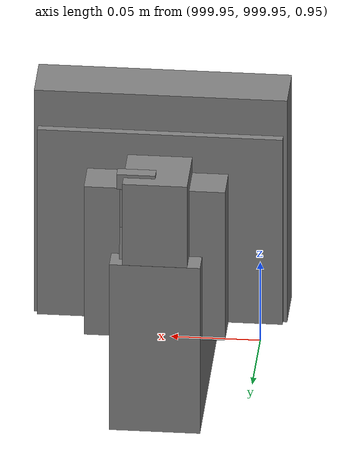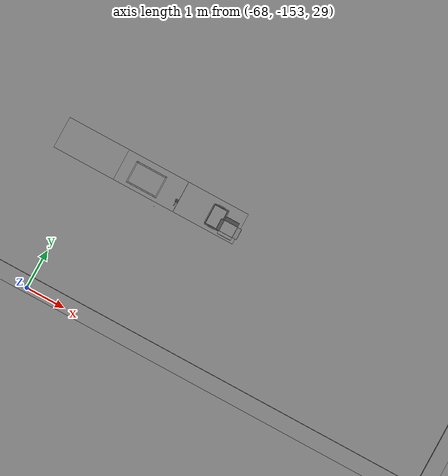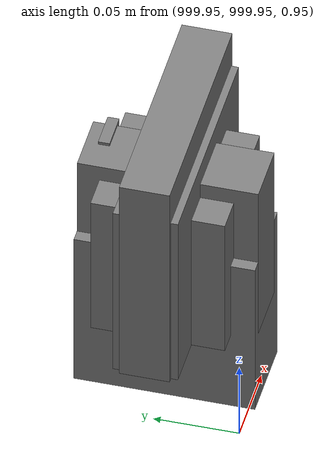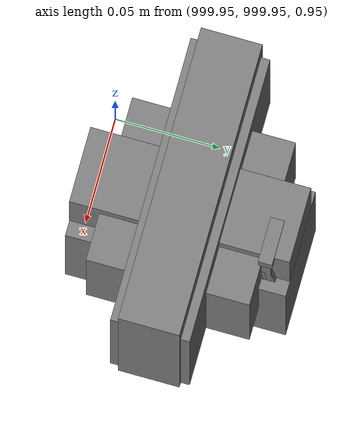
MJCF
<mujoco>
    <option gravity="0.000000000 0.000000000 -9.810000420" timestep="0.0049999999" integrator="implicitfast" density="1.225" viscosity="1.8000001e-05" noslip_iterations="10" iterations="100" sdf_iterations="50">
        <flag multiccd="disable"/>
    </option>
    <size memory="1000M"/>
    <compiler coordinate="local"/>
    <worldbody>
        <light cutoff="30" pos="0 1 1" dir="0 -1 -2"/>
        <light cutoff="30" pos="0 -1 1" dir="0 1 -2"/>
        <body pos="-66.395980835 -149.569305420 31.168781281" euler="-65.115837097 -80.253738403 51.843597412" mocap="true" name="spotlight1_SpotLight"/>
        <body pos="1000.000000000 1000.000000000 1.000000000" euler="0.000011953 0.000005123 -179.999984741" name="openloong_gripper_2f85_fix_base_usda_intel_box">
            <geom contype="1" conaffinity="1" density="1000" type="box" material="" rgba="0.500000000 0.500000000 0.500000000 1.000000000" solimp="0.899999976 0.949999988 0.001000000" friction="1.000000000 0.005000000 0.000100000" solref="0.020000000 1.000000000" margin="0" condim="3" group="0" pos="0.000000000 -0.000067139 0.000082284" quat="0.707106709 0.000000225 0.000000253 0.707106650" size="0.052800003 0.025300000 0.052800003" name="openloong_gripper_2f85_fix_base_usda_geom_3E286446_ECF3_4469_BB35_0F5CCE77A2DA"/>
            <freejoint name="openloong_gripper_2f85_fix_base_usda_intel_box_joint"/>
            <site size="0.005000000 0.005000000 0.005000000" rgba="0.500000000 0.500000000 0.500000000 1.000000000" pos="0.000000000 0.000000000 0.000000000" quat="0.999961913 0.008726500 0.000000000 0.000000000" group="0" type="sphere" name="openloong_gripper_2f85_fix_base_usda_intel_boxsite"/>
        </body>
        <body pos="1000.000000000 1000.000000000 1.000000000" euler="0.000000000 0.000000000 180.000000000" name="openloong_gripper_2f85_fix_base_usda_wifi_box">
            <geom contype="1" conaffinity="1" density="1000" type="box" material="" rgba="0.500000000 0.500000000 0.500000000 1.000000000" solimp="0.899999976 0.949999988 0.001000000" friction="1.000000000 0.005000000 0.000100000" solref="0.020000000 1.000000000" margin="0" condim="3" group="0" pos="0.000000000 0.000000000 0.058978677" quat="0.000000000 0.000000047 0.000000000 1.000000000" size="0.068499997 0.018999999 0.059000000" name="openloong_gripper_2f85_fix_base_usda_geom_414C0085_D409_4047_BC1A_85126A28AFFF"/>
            <freejoint name="openloong_gripper_2f85_fix_base_usda_wifi_box_joint"/>
            <site size="0.005000000 0.005000000 0.005000000" rgba="0.500000000 0.500000000 0.500000000 1.000000000" pos="0.000000000 0.000000000 0.000000000" quat="0.999961913 0.008726500 0.000000000 0.000000000" group="0" type="sphere" name="openloong_gripper_2f85_fix_base_usda_wifi_boxsite"/>
        </body>
        <body pos="1000.000000000 999.999938965 1.000000000" euler="0.000000000 0.000000000 180.000000000" name="openloong_gripper_2f85_fix_base_usda_intelcore_i5">
            <geom contype="1" conaffinity="1" density="1000" type="box" material="" rgba="0.500000000 0.500000000 0.500000000 1.000000000" solimp="0.899999976 0.949999988 0.001000000" friction="1.000000000 0.005000000 0.000100000" solref="0.020000000 1.000000000" margin="0" condim="3" group="0" pos="0.000000000 0.000000000 0.051722717" quat="0.707106709 0.000000000 0.000000000 -0.707106769" size="0.052800000 0.018080002 0.052800000" name="openloong_gripper_2f85_fix_base_usda_geom_9D276387_44C1_4C14_8777_18D1A77AA784"/>
            <freejoint name="openloong_gripper_2f85_fix_base_usda_intelcore_i5_joint"/>
            <site size="0.005000000 0.005000000 0.005000000" rgba="0.500000000 0.500000000 0.500000000 1.000000000" pos="0.000000000 0.000000000 0.000000000" quat="0.999961913 0.008726534 0.000000000 0.000000000" group="0" type="sphere" name="openloong_gripper_2f85_fix_base_usda_intelcore_i5site"/>
        </body>
        <body pos="-65.979560852 -149.177825928 31.171552658" euler="57.831203461 46.049808502 -116.394760132" mocap="true" name="spotlight2_SpotLight"/>
        <body pos="1000.000000000 1000.000000000 1.000000000" euler="0.000000000 0.000000000 180.000000000" name="openloong_gripper_2f85_fix_base_usda_cpu_fan">
            <geom contype="1" conaffinity="1" density="1000" type="box" material="" rgba="0.500000000 0.500000000 0.500000000 1.000000000" solimp="0.899999976 0.949999988 0.001000000" friction="1.000000000 0.005000000 0.000100000" solref="0.020000000 1.000000000" margin="0" condim="3" group="0" pos="0.000000000 0.000000000 0.070034981" quat="0.000000000 0.000000000 0.000000000 1.000000000" size="0.070700005 0.014699999 0.070700005" name="openloong_gripper_2f85_fix_base_usda_geom_4A6845B4_11E5_4EC1_9FDE_72E13F7F5CE5"/>
            <freejoint name="openloong_gripper_2f85_fix_base_usda_cpu_fan_joint"/>
            <site size="0.005000000 0.005000000 0.005000000" rgba="0.500000000 0.500000000 0.500000000 1.000000000" pos="0.000000000 0.000000000 0.000000000" quat="0.999961913 0.008726535 0.000000000 0.000000000" group="0" type="sphere" name="openloong_gripper_2f85_fix_base_usda_cpu_fancsite"/>
        </body>
        <body pos="1000.000000000 1000.000000000 1.000000000" euler="0.000000000 0.000000000 180.000000000" name="openloong_gripper_2f85_fix_base_usda_battery_01">
            <geom contype="1" conaffinity="1" density="1000" type="box" material="" rgba="0.500000000 0.500000000 0.500000000 1.000000000" solimp="0.899999976 0.949999988 0.001000000" friction="1.000000000 0.005000000 0.000100000" solref="0.020000000 1.000000000" margin="0" condim="3" group="0" pos="-0.011123657 -0.041940309 0.101691343" quat="1.000000000 0.000000000 0.000000000 0.000000000" size="0.010800000 0.003375000 0.004725000" name="openloong_gripper_2f85_fix_base_usda_geom_66025D76_F4FC_4360_9E22_65066E634CB9"/>
            <geom contype="1" conaffinity="1" density="1000" type="box" material="" rgba="0.500000000 0.500000000 0.500000000 1.000000000" solimp="0.899999976 0.949999988 0.001000000" friction="1.000000000 0.005000000 0.000100000" solref="0.020000000 1.000000000" margin="0" condim="3" group="0" pos="-0.010876465 -0.044247437 0.047066893" quat="0.998702705 -0.050920475 0.000000000 0.000000000" size="0.009450001 0.002700000 0.024975000" name="openloong_gripper_2f85_fix_base_usda_geom_8D42CFCF_6704_462D_AB46_844785FA67A9"/>
            <geom contype="1" conaffinity="1" density="1000" type="box" material="" rgba="0.500000000 0.500000000 0.500000000 1.000000000" solimp="0.899999976 0.949999988 0.001000000" friction="1.000000000 0.005000000 0.000100000" solref="0.020000000 1.000000000" margin="0" condim="3" group="0" pos="-0.001235962 -0.000659180 0.047381196" quat="1.000000000 0.000000000 0.000000000 0.000000000" size="0.039420001 0.039150000 0.047250003" name="openloong_gripper_2f85_fix_base_usda_geom_BBC891A3_5B0B_48FF_8A6A_CF051DB0CE02"/>
            <geom contype="1" conaffinity="1" density="1000" type="box" material="" rgba="0.500000000 0.500000000 0.500000000 1.000000000" solimp="0.899999976 0.949999988 0.001000000" friction="1.000000000 0.005000000 0.000100000" solref="0.020000000 1.000000000" margin="0" condim="3" group="0" pos="-0.010876465 -0.039138794 0.009851727" quat="1.000000000 0.000000000 0.000000000 0.000000000" size="0.009450001 0.010800000 0.013500000" name="openloong_gripper_2f85_fix_base_usda_geom_88788CC6_D272_4514_83C5_7EFAB6BB64B0"/>
            <geom contype="1" conaffinity="1" density="1000" type="box" material="" rgba="0.500000000 0.500000000 0.500000000 1.000000000" solimp="0.899999976 0.949999988 0.001000000" friction="1.000000000 0.005000000 0.000100000" solref="0.020000000 1.000000000" margin="0" condim="3" group="0" pos="-0.010876465 -0.041528322 0.071508206" quat="1.000000000 0.000000000 0.000000000 0.000000000" size="0.009450001 0.002700000 0.027000001" name="openloong_gripper_2f85_fix_base_usda_geom_B23FD1CB_62E2_40DE_ACE9_26868887A7D1"/>
            <freejoint name="openloong_gripper_2f85_fix_base_usda_battery_01_joint"/>
            <site size="0.005000000 0.005000000 0.005000000" rgba="0.500000000 0.500000000 0.500000000 1.000000000" pos="0.000000000 0.000000000 0.000000000" quat="0.999961913 0.008726500 0.000000000 0.000000000" group="0" type="sphere" name="openloong_gripper_2f85_fix_base_usda_battery_01site"/>
        </body>
        <body pos="-65.807579041 -148.933578491 31.171342850" euler="-127.196952820 2.330835342 -100.548141479" mocap="true" name="spotlight4_SpotLight"/>
        <body pos="-64.866622925 -149.383972168 30.183746338" euler="89.999984741 89.999946594 0.000000000" name="openloong_gripper_2f85_fix_base_usda_bluebox_01">
            <geom contype="1" conaffinity="1" density="1000" type="box" material="" rgba="0.500000000 0.500000000 0.500000000 1.000000000" solimp="0.899999976 0.949999988 0.001000000" friction="1.000000000 0.005000000 0.000100000" solref="0.020000000 1.000000000" margin="0" condim="3" group="0" pos="0.276580811 0.187225342 0.000068665" quat="0.707106948 0.000077471 0.707106352 0.000077486" size="0.100000001 0.057999998 0.010000000" name="openloong_gripper_2f85_fix_base_usda_geom_0F0014F1_75E5_4ED6_908F_64646A58C01C"/>
            <geom contype="1" conaffinity="1" density="1000" type="box" material="" rgba="0.500000000 0.500000000 0.500000000 1.000000000" solimp="0.899999976 0.949999988 0.001000000" friction="1.000000000 0.005000000 0.000100000" solref="0.020000000 1.000000000" margin="0" condim="3" group="0" pos="0.000000000 0.002883911 0.000000000" quat="0.999999881 0.000000000 0.000000000 0.000000000" size="0.254000008 0.003000000 0.172000006" name="openloong_gripper_2f85_fix_base_usda_geom_D083F294_B782_489C_B2A1_3C1991416EC2"/>
            <geom contype="1" conaffinity="1" density="1000" type="box" material="" rgba="0.500000000 0.500000000 0.500000000 1.000000000" solimp="0.899999976 0.949999988 0.001000000" friction="1.000000000 0.005000000 0.000100000" solref="0.020000000 1.000000000" margin="0" condim="3" group="0" pos="0.000000000 0.124874115 0.173484802" quat="0.999796331 0.020176515 -0.000000015 0.000000030" size="0.259999990 0.119999997 0.007000000" name="openloong_gripper_2f85_fix_base_usda_geom_18956782_8085_479D_8F0C_1E870641853E"/>
            <geom contype="1" conaffinity="1" density="1000" type="box" material="" rgba="0.500000000 0.500000000 0.500000000 1.000000000" solimp="0.899999976 0.949999988 0.001000000" friction="1.000000000 0.005000000 0.000100000" solref="0.020000000 1.000000000" margin="0" condim="3" group="0" pos="0.000000000 0.124874115 -0.173469543" quat="0.999796331 -0.020176545 -0.000000015 0.000000000" size="0.259999990 0.119999997 0.007000000" name="openloong_gripper_2f85_fix_base_usda_geom_ECF67A44_B004_48AF_8348_7FD753E1635D"/>
            <geom contype="1" conaffinity="1" density="1000" type="box" material="" rgba="0.500000000 0.500000000 0.500000000 1.000000000" solimp="0.899999976 0.949999988 0.001000000" friction="1.000000000 0.005000000 0.000100000" solref="0.020000000 1.000000000" margin="0" condim="3" group="0" pos="0.000000000 0.214008331 0.188980103" quat="0.999912977 0.013176724 0.000000015 0.000000000" size="0.259999990 0.029999999 0.012500000" name="openloong_gripper_2f85_fix_base_usda_geom_76BAA375_0C54_4183_AAA6_15D6C751AF6A"/>
            <geom contype="1" conaffinity="1" density="1000" type="box" material="" rgba="0.500000000 0.500000000 0.500000000 1.000000000" solimp="0.899999976 0.949999988 0.001000000" friction="1.000000000 0.005000000 0.000100000" solref="0.020000000 1.000000000" margin="0" condim="3" group="0" pos="-0.258361816 0.125289917 0.001876831" quat="0.702796936 -0.020792112 0.710783124 0.020769298" size="0.189999998 0.119999997 0.009000000" name="openloong_gripper_2f85_fix_base_usda_geom_33FF6F29_5AA7_47DB_8E2E_6C20508A3196"/>
            <geom contype="1" conaffinity="1" density="1000" type="box" material="" rgba="0.500000000 0.500000000 0.500000000 1.000000000" solimp="0.899999976 0.949999988 0.001000000" friction="1.000000000 0.005000000 0.000100000" solref="0.020000000 1.000000000" margin="0" condim="3" group="0" pos="0.000000000 0.214008331 -0.188980103" quat="0.999912977 -0.013176769 0.000000030 0.000000015" size="0.259999990 0.029999999 0.012500000" name="openloong_gripper_2f85_fix_base_usda_geom_EBD25B8E_09B7_4CC5_8EAE_671F08378DF2"/>
            <geom contype="1" conaffinity="1" density="1000" type="box" material="" rgba="0.500000000 0.500000000 0.500000000 1.000000000" solimp="0.899999976 0.949999988 0.001000000" friction="1.000000000 0.005000000 0.000100000" solref="0.020000000 1.000000000" margin="0" condim="3" group="0" pos="-0.276611328 0.187225342 0.000068665" quat="0.707106650 0.000077441 0.707106709 0.000077456" size="0.100000001 0.057999998 0.010000000" name="openloong_gripper_2f85_fix_base_usda_geom_A905FC33_272D_44F2_9A75_128F9F3D7D3B"/>
            <geom contype="1" conaffinity="1" density="1000" type="box" material="" rgba="0.500000000 0.500000000 0.500000000 1.000000000" solimp="0.899999976 0.949999988 0.001000000" friction="1.000000000 0.005000000 0.000100000" solref="0.020000000 1.000000000" margin="0" condim="3" group="0" pos="0.258331299 0.125289917 0.001876831" quat="0.702851415 0.018856421 0.710823774 -0.019329369" size="0.189999998 0.119999997 0.009000000" name="openloong_gripper_2f85_fix_base_usda_geom_58182810_705D_4547_98D8_DF050DBD6B74"/>
            <freejoint name="openloong_gripper_2f85_fix_base_usda_bluebox_01_joint"/>
            <site size="0.005000000 0.005000000 0.005000000" rgba="0.500000000 0.500000000 0.500000000 1.000000000" pos="0.000000000 0.000000000 0.000000000" quat="0.999961913 0.008726534 0.000000000 0.000000000" group="0" type="sphere" name="openloong_gripper_2f85_fix_base_usda_bluebox_01site"/>
        </body>
        <body pos="-64.496299744 -149.491867065 30.235729218" euler="0.000000000 0.000000000 89.999946594" name="openloong_gripper_2f85_fix_base_usda_cardboardbox_01">
            <geom contype="1" conaffinity="1" density="1000" type="box" material="" rgba="0.500000000 0.500000000 0.500000000 1.000000000" solimp="0.899999976 0.949999988 0.001000000" friction="1.000000000 0.005000000 0.000100000" solref="0.020000000 1.000000000" margin="0" condim="3" group="0" pos="-0.003166199 -0.004086494 0.005052090" quat="1.000000000 0.000000000 0.000000000 0.000000000" size="0.142499998 0.177500010 0.005000000" name="openloong_gripper_2f85_fix_base_usda_geom_BDA3A568_5F91_4000_AB4C_E0EF145504A7"/>
            <geom contype="1" conaffinity="1" density="1000" type="box" material="" rgba="0.500000000 0.500000000 0.500000000 1.000000000" solimp="0.899999976 0.949999988 0.001000000" friction="1.000000000 0.005000000 0.000100000" solref="0.020000000 1.000000000" margin="0" condim="3" group="0" pos="-0.003166199 0.170316696 0.150570869" quat="1.000000000 0.000000000 0.000000000 0.000000000" size="0.142499998 0.005000000 0.149999991" name="openloong_gripper_2f85_fix_base_usda_geom_E7BB6637_5CE5_4386_A290_8C76266066F0"/>
            <geom contype="1" conaffinity="1" density="1000" type="box" material="" rgba="0.500000000 0.500000000 0.500000000 1.000000000" solimp="0.899999976 0.949999988 0.001000000" friction="1.000000000 0.005000000 0.000100000" solref="0.020000000 1.000000000" margin="0" condim="3" group="0" pos="-0.147399902 -0.005307198 0.150570869" quat="1.000000000 0.000000000 0.000000000 0.000000000" size="0.005000000 0.177500010 0.149999991" name="openloong_gripper_2f85_fix_base_usda_geom_166F51A7_932E_4D6F_B5EA_94DEE599CCC8"/>
            <geom contype="1" conaffinity="1" density="1000" type="box" material="" rgba="0.500000000 0.500000000 0.500000000 1.000000000" solimp="0.899999976 0.949999988 0.001000000" friction="1.000000000 0.005000000 0.000100000" solref="0.020000000 1.000000000" margin="0" condim="3" group="0" pos="0.140275955 -0.005307198 0.150570869" quat="1.000000000 0.000000000 0.000000000 0.000000000" size="0.005000000 0.177500010 0.149999991" name="openloong_gripper_2f85_fix_base_usda_geom_DB684432_B6E9_418A_A71E_FA72A0459260"/>
            <geom contype="1" conaffinity="1" density="1000" type="box" material="" rgba="0.500000000 0.500000000 0.500000000 1.000000000" solimp="0.899999976 0.949999988 0.001000000" friction="1.000000000 0.005000000 0.000100000" solref="0.020000000 1.000000000" margin="0" condim="3" group="0" pos="-0.003166199 -0.181550980 0.150570869" quat="1.000000000 0.000000000 0.000000000 0.000000000" size="0.142499998 0.005000000 0.149999991" name="openloong_gripper_2f85_fix_base_usda_geom_E48B9082_1136_453D_A48A_2546AB7FE9BA"/>
            <freejoint name="openloong_gripper_2f85_fix_base_usda_cardboardbox_01_joint"/>
            <site size="0.005000000 0.005000000 0.005000000" rgba="0.500000000 0.500000000 0.500000000 1.000000000" pos="0.000000000 0.000000000 0.000000000" quat="0.999961913 0.008726535 0.000000000 0.000000000" group="0" type="sphere" name="openloong_gripper_2f85_fix_base_usda_site_3E84BB5C_D816_44F8_BD21_BF6346FE3A08"/>
            <body pos="0.139160156 -0.004048347 0.301930904" euler="-179.999954224 49.383502960 179.999954224" name="openloong_gripper_2f85_fix_base_usda_A1_006">
                <geom contype="1" conaffinity="1" density="1000" type="box" material="" rgba="0.500000000 0.500000000 0.500000000 1.000000000" solimp="0.899999976 0.949999988 0.001000000" friction="1.000000000 0.005000000 0.000100000" solref="0.020000000 1.000000000" margin="0" condim="3" group="0" pos="-0.071587563 0.000009537 0.001745224" quat="0.999999881 0.000000000 0.000000000 0.000000000" size="0.071249999 0.179999992 0.002500000" name="openloong_gripper_2f85_fix_base_usda_geom_60ED565A_6CCE_4E5C_AD90_2AAADEB41FCA"/>
                <joint armature="0" stiffness="0.07" damping="0.0099999998" axis="0.000000 1.000000 0.000000" type="hinge" name="openloong_gripper_2f85_fix_base_usda_A1_006"/>
            </body>
            <body pos="-0.145902634 -0.004086494 0.301938057" euler="-180.000000000 -60.000011444 -180.000000000" name="openloong_gripper_2f85_fix_base_usda_A2_006">
                <geom contype="1" conaffinity="1" density="1000" type="box" material="" rgba="0.500000000 0.500000000 0.500000000 1.000000000" solimp="0.899999976 0.949999988 0.001000000" friction="1.000000000 0.005000000 0.000100000" solref="0.020000000 1.000000000" margin="0" condim="3" group="0" pos="0.071268082 0.000009537 0.002717972" quat="0.000002921 0.000000000 -0.000000030 0.999999881" size="0.071249999 0.179999992 0.002500000" name="openloong_gripper_2f85_fix_base_usda_geom_84838C5C_A215_4BB4_9236_D19627209A76"/>
                <joint armature="0" stiffness="0.07" damping="0.0099999998" axis="0.000000 1.000000 0.000000" type="hinge" name="openloong_gripper_2f85_fix_base_usda_A2_006"/>
            </body>
            <body pos="-0.003385544 0.175991058 0.301930904" euler="-125.858116150 -0.000004561 0.000002331" name="openloong_gripper_2f85_fix_base_usda_B2_006">
                <geom contype="1" conaffinity="1" density="1000" type="box" material="" rgba="0.500000000 0.500000000 0.500000000 1.000000000" solimp="0.899999976 0.949999988 0.001000000" friction="1.000000000 0.005000000 0.000100000" solref="0.020000000 1.000000000" margin="0" condim="3" group="0" pos="0.000009537 -0.070939064 -0.002470016" quat="0.999614120 0.027776197 -0.000000015 0.000000030" size="0.137500003 0.064999998 0.005000000" name="openloong_gripper_2f85_fix_base_usda_geom_02A3B8EE_1824_4F4A_ADFC_05B8B5474B5D"/>
                <joint armature="0" stiffness="0.07" damping="0.0099999998" axis="1.000000 0.000000 0.000000" type="hinge" name="openloong_gripper_2f85_fix_base_usda_B2_006"/>
            </body>
            <body pos="-0.003385544 -0.184140205 0.301938057" euler="147.805557251 0.000000000 0.000000000" name="openloong_gripper_2f85_fix_base_usda_B1_006">
                <geom contype="1" conaffinity="1" density="1000" type="box" material="" rgba="0.500000000 0.500000000 0.500000000 1.000000000" solimp="0.899999976 0.949999988 0.001000000" friction="1.000000000 0.005000000 0.000100000" solref="0.020000000 1.000000000" margin="0" condim="3" group="0" pos="-0.000028610 0.070202351 -0.002703667" quat="0.999614179 -0.027776167 0.000000000 0.000000000" size="0.137500003 0.064999998 0.005000000" name="openloong_gripper_2f85_fix_base_usda_geom_106E6104_FA84_445E_B962_8890A6463D4A"/>
                <joint armature="0" stiffness="0.07" damping="0.0099999998" axis="1.000000 0.000000 0.000000" type="hinge" name="openloong_gripper_2f85_fix_base_usda_B1_006"/>
            </body>
        </body>
        <body pos="-65.882858276 -149.481979370 30.229999542" euler="-64.487716675 0.000000000 0.000000000" name="openloong_gripper_2f85_fix_base_usda_Barcode">
            <geom contype="1" conaffinity="1" density="1000" type="box" material="" rgba="0.500000000 0.500000000 0.500000000 1.000000000" solimp="0.899999976 0.949999988 0.001000000" friction="1.000000000 0.005000000 0.000100000" solref="0.020000000 1.000000000" margin="0" condim="3" group="0" pos="0.000000000 0.013038635 0.001419067" quat="0.000000000 0.000000000 0.000000000 1.000000119" size="0.034000002 0.010000000 0.017999999" name="openloong_gripper_2f85_fix_base_usda_geom_CF313AF4_9025_434A_9DD7_C6B37741A7B3"/>
            <geom contype="1" conaffinity="1" density="1000" type="box" material="" rgba="0.500000000 0.500000000 0.500000000 1.000000000" solimp="0.899999976 0.949999988 0.001000000" friction="1.000000000 0.005000000 0.000100000" solref="0.020000000 1.000000000" margin="0" condim="3" group="0" pos="0.000000000 -0.035301208 -0.007095337" quat="0.000000000 0.000000000 -0.043619365 0.999048233" size="0.028999999 0.010000000 0.020000000" name="openloong_gripper_2f85_fix_base_usda_geom_D7C74E52_ADBE_4CD9_B37E_CAD3AD78275E"/>
            <geom contype="1" conaffinity="1" density="1000" type="box" material="" rgba="0.500000000 0.500000000 0.500000000 1.000000000" solimp="0.899999976 0.949999988 0.001000000" friction="1.000000000 0.005000000 0.000100000" solref="0.020000000 1.000000000" margin="0" condim="3" group="0" pos="0.000000000 -0.043411255 -0.011749268" quat="0.922262907 0.386563420 0.000000000 0.000000000" size="0.026000001 0.010000000 0.020000000" name="openloong_gripper_2f85_fix_base_usda_geom_D7E8DED7_4011_4E06_BF97_C5E6F7FBA36F"/>
            <geom contype="1" conaffinity="1" density="1000" type="box" material="" rgba="0.500000000 0.500000000 0.500000000 1.000000000" solimp="0.899999976 0.949999988 0.001000000" friction="1.000000000 0.005000000 0.000100000" solref="0.020000000 1.000000000" margin="0" condim="3" group="0" pos="0.000000000 -0.016967773 -0.031860352" quat="0.000000000 0.000000000 0.000000000 1.000000119" size="0.008000000 0.010000000 0.013000000" name="openloong_gripper_2f85_fix_base_usda_geom_84F4A6BC_5CEF_4C33_B1A1_5BDE7548F63E"/>
            <geom contype="1" conaffinity="1" density="1000" type="box" material="" rgba="0.500000000 0.500000000 0.500000000 1.000000000" solimp="0.899999976 0.949999988 0.001000000" friction="1.000000000 0.005000000 0.000100000" solref="0.020000000 1.000000000" margin="0" condim="3" group="0" pos="0.000000000 -0.001869202 0.000312805" quat="0.953716993 0.300705761 0.000000000 0.000000000" size="0.032000002 0.010000000 0.018999999" name="openloong_gripper_2f85_fix_base_usda_geom_71C53D37_C0DE_46A3_AB5F_BE91BA72F6BB"/>
            <geom contype="1" conaffinity="1" density="1000" type="box" material="" rgba="0.500000000 0.500000000 0.500000000 1.000000000" solimp="0.899999976 0.949999988 0.001000000" friction="1.000000000 0.005000000 0.000100000" solref="0.020000000 1.000000000" margin="0" condim="3" group="0" pos="0.000000000 -0.019531250 -0.003173828" quat="0.953716993 0.300705761 0.000000000 0.000000000" size="0.030999999 0.010000000 0.020000000" name="openloong_gripper_2f85_fix_base_usda_geom_FC57DA5A_79FE_429B_8010_D54DD05700EF"/>
            <geom contype="1" conaffinity="1" density="1000" type="box" material="" rgba="0.500000000 0.500000000 0.500000000 1.000000000" solimp="0.899999976 0.949999988 0.001000000" friction="1.000000000 0.005000000 0.000100000" solref="0.020000000 1.000000000" margin="0" condim="3" group="0" pos="0.000000000 -0.035301208 -0.007095337" quat="0.953716993 0.300705761 0.000000000 0.000000000" size="0.028999999 0.010000000 0.020000000" name="openloong_gripper_2f85_fix_base_usda_geom_C6E1BD69_F057_4431_BD8B_9AE7DD21A572"/>
            <geom contype="1" conaffinity="1" density="1000" type="box" material="" rgba="0.500000000 0.500000000 0.500000000 1.000000000" solimp="0.899999976 0.949999988 0.001000000" friction="1.000000000 0.005000000 0.000100000" solref="0.020000000 1.000000000" margin="0" condim="3" group="0" pos="0.000000000 -0.042617798 -0.071121216" quat="0.000000000 0.000000000 0.000000000 1.000000119" size="0.013000000 0.021000000 0.059999999" name="openloong_gripper_2f85_fix_base_usda_geom_93F47033_5EBD_4460_AB86_F2AE0B63F7BC"/>
            <freejoint name="openloong_gripper_2f85_fix_base_usda_Barcode_joint"/>
            <site size="0.005000000 0.005000000 0.005000000" rgba="0.500000000 0.500000000 0.500000000 1.000000000" pos="0.000000000 0.000000000 0.000000000" quat="1.000000000 0.000000000 0.000000000 0.000000000" group="0" type="sphere" name="openloong_gripper_2f85_fix_base_usda_Barcode_site"/>
        </body>
        <body pos="-66.745018005 -149.392349243 30.184000015" euler="0.000000000 0.000000000 89.999946594" name="[22333466089558]_Basket_01">
            <geom contype="1" conaffinity="1" density="1000" type="box" material="" rgba="0.500000000 0.500000000 0.500000000 1.000000000" solimp="0.899999976 0.949999988 0.001000000" friction="1.000000000 0.005000000 0.000100000" solref="0.020000000 1.000000000" margin="0" condim="3" group="0" pos="-0.052425385 0.389207840 0.089787483" quat="0.707107008 0.000000000 0.000000000 0.707106411" size="0.014249999 0.014249999 0.059999999" name="[22333466089558]_geom_13095B3B_EECA_4164_B0D2_A16ADA853C94"/>
            <geom contype="1" conaffinity="1" density="1000" type="box" material="" rgba="0.500000000 0.500000000 0.500000000 1.000000000" solimp="0.899999976 0.949999988 0.001000000" friction="1.000000000 0.005000000 0.000100000" solref="0.020000000 1.000000000" margin="0" condim="3" group="0" pos="0.264015198 -0.133043289 0.089787483" quat="0.707107008 0.000000000 0.000000000 0.707106411" size="0.014249999 0.014249999 0.059999999" name="[22333466089558]_geom_41534B81_0884_47F1_B8DD_4D4256C8F3CE"/>
            <geom contype="1" conaffinity="1" density="1000" type="box" material="" rgba="0.500000000 0.500000000 0.500000000 1.000000000" solimp="0.899999976 0.949999988 0.001000000" friction="1.000000000 0.005000000 0.000100000" solref="0.020000000 1.000000000" margin="0" condim="3" group="0" pos="-0.264015198 -0.265548706 0.089793205" quat="0.707107008 0.000000000 0.000000000 0.707106411" size="0.014249999 0.014249999 0.059999999" name="[22333466089558]_geom_69B2B8A1_6650_428E_AFB6_98F39F8DDC15"/>
            <geom contype="1" conaffinity="1" density="1000" type="box" material="" rgba="0.500000000 0.500000000 0.500000000 1.000000000" solimp="0.899999976 0.949999988 0.001000000" friction="1.000000000 0.005000000 0.000100000" solref="0.020000000 1.000000000" margin="0" condim="3" group="0" pos="-0.160263062 -0.389322281 0.089793205" quat="0.707107008 0.000000000 0.000000000 0.707106411" size="0.014249999 0.014249999 0.059999999" name="[22333466089558]_geom_080AE2A9_B0B9_4F7B_9178_75EEC5A719E7"/>
            <geom contype="1" conaffinity="1" density="1000" type="box" material="" rgba="0.500000000 0.500000000 0.500000000 1.000000000" solimp="0.899999976 0.949999988 0.001000000" friction="1.000000000 0.005000000 0.000100000" solref="0.020000000 1.000000000" margin="0" condim="3" group="0" pos="0.162265778 -0.389322281 0.089787483" quat="0.707107008 0.000000000 0.000000000 0.707106411" size="0.014249999 0.014249999 0.059999999" name="[22333466089558]_geom_B7E2AFDB_941C_4AC1_8895_5C06D8D5A8B3"/>
            <geom contype="1" conaffinity="1" density="1000" type="box" material="" rgba="0.500000000 0.500000000 0.500000000 1.000000000" solimp="0.899999976 0.949999988 0.001000000" friction="1.000000000 0.005000000 0.000100000" solref="0.020000000 1.000000000" margin="0" condim="3" group="0" pos="0.264015198 0.389207840 0.089787483" quat="0.707107008 0.000000000 0.000000000 0.707106411" size="0.014249999 0.014249999 0.059999999" name="[22333466089558]_geom_693AA794_ED26_478E_BC08_C39B7C09709A"/>
            <geom contype="1" conaffinity="1" density="1000" type="box" material="" rgba="0.500000000 0.500000000 0.500000000 1.000000000" solimp="0.899999976 0.949999988 0.001000000" friction="1.000000000 0.005000000 0.000100000" solref="0.020000000 1.000000000" margin="0" condim="3" group="0" pos="-0.264015198 -0.133043289 0.089793205" quat="0.707107008 0.000000000 0.000000000 0.707106411" size="0.014249999 0.014249999 0.059999999" name="[22333466089558]_geom_F2350BC3_BFE3_4DCE_9041_024E24225C1C"/>
            <geom contype="1" conaffinity="1" density="1000" type="box" material="" rgba="0.500000000 0.500000000 0.500000000 1.000000000" solimp="0.899999976 0.949999988 0.001000000" friction="1.000000000 0.005000000 0.000100000" solref="0.020000000 1.000000000" margin="0" condim="3" group="0" pos="-0.264026642 0.269256592 0.089793205" quat="0.707107008 0.000000000 0.000000000 0.707106411" size="0.014249999 0.014249999 0.059999999" name="[22333466089558]_geom_3AA4E853_4DF9_4815_8E5F_9684F3084CC7"/>
            <geom contype="1" conaffinity="1" density="1000" type="box" material="" rgba="0.500000000 0.500000000 0.500000000 1.000000000" solimp="0.899999976 0.949999988 0.001000000" friction="1.000000000 0.005000000 0.000100000" solref="0.020000000 1.000000000" margin="0" condim="3" group="0" pos="0.054462433 0.389207840 0.089787483" quat="0.707107008 0.000000000 0.000000000 0.707106411" size="0.014249999 0.014249999 0.059999999" name="[22333466089558]_geom_FA94522F_8791_463E_97EF_2F844FB93FE5"/>
            <geom contype="1" conaffinity="1" density="1000" type="box" material="" rgba="0.500000000 0.500000000 0.500000000 1.000000000" solimp="0.899999976 0.949999988 0.001000000" friction="1.000000000 0.005000000 0.000100000" solref="0.020000000 1.000000000" margin="0" condim="3" group="0" pos="0.054462433 -0.389322281 0.089787483" quat="0.707107008 0.000000000 0.000000000 0.707106411" size="0.014249999 0.014249999 0.059999999" name="[22333466089558]_geom_B9017F53_1D5A_49F9_8A18_89DCF0D48339"/>
            <geom contype="1" conaffinity="1" density="1000" type="box" material="" rgba="0.500000000 0.500000000 0.500000000 1.000000000" solimp="0.899999976 0.949999988 0.001000000" friction="1.000000000 0.005000000 0.000100000" solref="0.020000000 1.000000000" margin="0" condim="3" group="0" pos="0.264015198 0.269256592 0.089793205" quat="0.707107008 0.000000000 0.000000000 0.707106411" size="0.014249999 0.014249999 0.059999999" name="[22333466089558]_geom_9736CADA_2C8E_4713_8FA8_F18DACF34D35"/>
            <geom contype="1" conaffinity="1" density="1000" type="box" material="" rgba="0.500000000 0.500000000 0.500000000 1.000000000" solimp="0.899999976 0.949999988 0.001000000" friction="1.000000000 0.005000000 0.000100000" solref="0.020000000 1.000000000" margin="0" condim="3" group="0" pos="0.264015198 -0.389322281 0.089787483" quat="0.707107008 0.000000000 0.000000000 0.707106411" size="0.014249999 0.014249999 0.059999999" name="[22333466089558]_geom_9C24D5C7_644C_4E8C_8285_319072AF71C5"/>
            <geom contype="1" conaffinity="1" density="1000" type="box" material="" rgba="0.500000000 0.500000000 0.500000000 1.000000000" solimp="0.899999976 0.949999988 0.001000000" friction="1.000000000 0.005000000 0.000100000" solref="0.020000000 1.000000000" margin="0" condim="3" group="0" pos="0.000000000 0.000000000 0.015998840" quat="0.707107008 0.000000000 0.000000000 0.707106411" size="0.403499991 0.279000014 0.015750000" name="[22333466089558]_geom_BF839DE6_DE96_4F83_A2AE_FEDE8D863703"/>
            <geom contype="1" conaffinity="1" density="1000" type="box" material="" rgba="0.500000000 0.500000000 0.500000000 1.000000000" solimp="0.899999976 0.949999988 0.001000000" friction="1.000000000 0.005000000 0.000100000" solref="0.020000000 1.000000000" margin="0" condim="3" group="0" pos="0.000000000 -0.389476776 0.163619041" quat="0.707107008 0.000000000 0.000000000 0.707106411" size="0.015000000 0.277500004 0.015750000" name="[22333466089558]_geom_DC2026B2_0275_4FEB_B200_687F464841FD"/>
            <geom contype="1" conaffinity="1" density="1000" type="box" material="" rgba="0.500000000 0.500000000 0.500000000 1.000000000" solimp="0.899999976 0.949999988 0.001000000" friction="1.000000000 0.005000000 0.000100000" solref="0.020000000 1.000000000" margin="0" condim="3" group="0" pos="0.162265778 0.389207840 0.089787483" quat="0.707107008 0.000000000 0.000000000 0.707106411" size="0.014249999 0.014249999 0.059999999" name="[22333466089558]_geom_0656583A_3B4C_44C5_8D19_C155929173EB"/>
            <geom contype="1" conaffinity="1" density="1000" type="box" material="" rgba="0.500000000 0.500000000 0.500000000 1.000000000" solimp="0.899999976 0.949999988 0.001000000" friction="1.000000000 0.005000000 0.000100000" solref="0.020000000 1.000000000" margin="0" condim="3" group="0" pos="0.000000000 0.389471054 0.163619041" quat="0.707107008 0.000000000 0.000000000 0.707106411" size="0.015000000 0.277500004 0.015750000" name="[22333466089558]_geom_75A77340_0F76_4B63_AD04_A1C17AB391A4"/>
            <geom contype="1" conaffinity="1" density="1000" type="box" material="" rgba="0.500000000 0.500000000 0.500000000 1.000000000" solimp="0.899999976 0.949999988 0.001000000" friction="1.000000000 0.005000000 0.000100000" solref="0.020000000 1.000000000" margin="0" condim="3" group="0" pos="-0.263511658 0.000000000 0.163619041" quat="0.707107008 0.000000000 0.000000000 0.707106411" size="0.403499991 0.015000000 0.015750000" name="[22333466089558]_geom_DFBAC6FF_5FBC_4923_8237_63EBD04BBE44"/>
            <geom contype="1" conaffinity="1" density="1000" type="box" material="" rgba="0.500000000 0.500000000 0.500000000 1.000000000" solimp="0.899999976 0.949999988 0.001000000" friction="1.000000000 0.005000000 0.000100000" solref="0.020000000 1.000000000" margin="0" condim="3" group="0" pos="-0.264015198 0.141334534 0.089793205" quat="0.707107008 0.000000000 0.000000000 0.707106411" size="0.014249999 0.014249999 0.059999999" name="[22333466089558]_geom_71FF91FA_33D9_4258_802E_8BC0C065199B"/>
            <geom contype="1" conaffinity="1" density="1000" type="box" material="" rgba="0.500000000 0.500000000 0.500000000 1.000000000" solimp="0.899999976 0.949999988 0.001000000" friction="1.000000000 0.005000000 0.000100000" solref="0.020000000 1.000000000" margin="0" condim="3" group="0" pos="0.264015198 -0.265548706 0.089787483" quat="0.707107008 0.000000000 0.000000000 0.707106411" size="0.014249999 0.014249999 0.059999999" name="[22333466089558]_geom_6BAAC5E5_8458_4BA3_8839_00250ED6B2C4"/>
            <geom contype="1" conaffinity="1" density="1000" type="box" material="" rgba="0.500000000 0.500000000 0.500000000 1.000000000" solimp="0.899999976 0.949999988 0.001000000" friction="1.000000000 0.005000000 0.000100000" solref="0.020000000 1.000000000" margin="0" condim="3" group="0" pos="-0.160263062 0.389207840 0.089787483" quat="0.707107008 0.000000000 0.000000000 0.707106411" size="0.014249999 0.014249999 0.059999999" name="[22333466089558]_geom_36AC03C6_311E_4FA1_A2F0_53EF6E5ACAE3"/>
            <geom contype="1" conaffinity="1" density="1000" type="box" material="" rgba="0.500000000 0.500000000 0.500000000 1.000000000" solimp="0.899999976 0.949999988 0.001000000" friction="1.000000000 0.005000000 0.000100000" solref="0.020000000 1.000000000" margin="0" condim="3" group="0" pos="-0.052425385 -0.389322281 0.089787483" quat="0.707107008 0.000000000 0.000000000 0.707106411" size="0.014249999 0.014249999 0.059999999" name="[22333466089558]_geom_4E5726A2_704E_42CE_A5AB_770AEE0FEBEA"/>
            <geom contype="1" conaffinity="1" density="1000" type="box" material="" rgba="0.500000000 0.500000000 0.500000000 1.000000000" solimp="0.899999976 0.949999988 0.001000000" friction="1.000000000 0.005000000 0.000100000" solref="0.020000000 1.000000000" margin="0" condim="3" group="0" pos="-0.264026642 -0.389322281 0.089793205" quat="0.707107008 0.000000000 0.000000000 0.707106411" size="0.014249999 0.014249999 0.059999999" name="[22333466089558]_geom_1C2AD5A6_3954_46B6_BC5B_A6941684C062"/>
            <geom contype="1" conaffinity="1" density="1000" type="box" material="" rgba="0.500000000 0.500000000 0.500000000 1.000000000" solimp="0.899999976 0.949999988 0.001000000" friction="1.000000000 0.005000000 0.000100000" solref="0.020000000 1.000000000" margin="0" condim="3" group="0" pos="0.264015198 0.141334534 0.089787483" quat="0.707107008 0.000000000 0.000000000 0.707106411" size="0.014249999 0.014249999 0.059999999" name="[22333466089558]_geom_A4DC09B4_D21E_43ED_995F_8F1E054645E8"/>
            <geom contype="1" conaffinity="1" density="1000" type="box" material="" rgba="0.500000000 0.500000000 0.500000000 1.000000000" solimp="0.899999976 0.949999988 0.001000000" friction="1.000000000 0.005000000 0.000100000" solref="0.020000000 1.000000000" margin="0" condim="3" group="0" pos="-0.264015198 0.389207840 0.089793205" quat="0.707107008 0.000000000 0.000000000 0.707106411" size="0.014249999 0.014249999 0.059999999" name="[22333466089558]_geom_92BB42B3_7133_4803_996F_A15CF38CCF9E"/>
            <geom contype="1" conaffinity="1" density="1000" type="box" material="" rgba="0.500000000 0.500000000 0.500000000 1.000000000" solimp="0.899999976 0.949999988 0.001000000" friction="1.000000000 0.005000000 0.000100000" solref="0.020000000 1.000000000" margin="0" condim="3" group="0" pos="0.264015198 0.004480362 0.089787483" quat="0.707107008 0.000000000 0.000000000 0.707106411" size="0.014249999 0.014249999 0.059999999" name="[22333466089558]_geom_A2361471_DD59_40FD_AE15_B22307FDE165"/>
            <geom contype="1" conaffinity="1" density="1000" type="box" material="" rgba="0.500000000 0.500000000 0.500000000 1.000000000" solimp="0.899999976 0.949999988 0.001000000" friction="1.000000000 0.005000000 0.000100000" solref="0.020000000 1.000000000" margin="0" condim="3" group="0" pos="0.263694763 -0.000011444 0.163619041" quat="0.707107008 0.000000000 0.000000000 0.707106411" size="0.403499991 0.015000000 0.015750000" name="[22333466089558]_geom_7F8E0055_1CAB_40B1_BBA7_CF4CBC38D4F3"/>
            <geom contype="1" conaffinity="1" density="1000" type="box" material="" rgba="0.500000000 0.500000000 0.500000000 1.000000000" solimp="0.899999976 0.949999988 0.001000000" friction="1.000000000 0.005000000 0.000100000" solref="0.020000000 1.000000000" margin="0" condim="3" group="0" pos="-0.264015198 0.004480362 0.089793205" quat="0.707107008 0.000000000 0.000000000 0.707106411" size="0.014249999 0.014249999 0.059999999" name="[22333466089558]_geom_98ECE524_4682_43D7_B53E_197435E67C37"/>
            <freejoint name="[22333466089558]_joint_3C6E6F3A_A3E6_433A_AE29_BC59B3D75A65"/>
        </body>
        <body pos="0.000000000 0.000000000 0.000000000" euler="0.000000000 0.000000000 0.000000000" name="Static Objects_Static Objects">
            <geom contype="1" conaffinity="1" density="1000" type="box" material="" rgba="0.500000000 0.500000000 0.500000000 1.000000000" solimp="0.899999976 0.949999988 0.001000000" friction="1.000000000 0.005000000 0.000100000" solref="0.020000000 1.000000000" margin="0" condim="3" group="0" pos="-67.544113159 -149.365814209 29.727830887" quat="0.500000417 0.499999970 0.499999553 0.499999970" size="0.381000012 0.319999993 0.041000001" name="Static Objects_geom_1B68B7B3_452F_49E2_8A90_66E0036DAD94"/>
            <geom contype="1" conaffinity="1" density="1000" type="box" material="" rgba="0.500000000 0.500000000 0.500000000 1.000000000" solimp="0.899999976 0.949999988 0.001000000" friction="1.000000000 0.005000000 0.000100000" solref="0.020000000 1.000000000" margin="0" condim="3" group="0" pos="-68.239501953 -149.365814209 30.086868286" quat="0.500000417 0.499999970 0.499999553 0.499999970" size="0.370999992 0.039500002 0.745000005" name="Static Objects_geom_CC7F3483_3F0E_455C_AFC8_515823A4D12D"/>
            <geom contype="1" conaffinity="1" density="1000" type="box" material="" rgba="0.500000000 0.500000000 0.500000000 1.000000000" solimp="0.899999976 0.949999988 0.001000000" friction="1.000000000 0.005000000 0.000100000" solref="0.020000000 1.000000000" margin="0" condim="3" group="0" pos="-68.239501953 -149.365814209 30.147235870" quat="0.500000417 0.499999970 0.499999553 0.499999970" size="0.400000006 0.022000000 0.800000012" name="Static Objects_geom_76DBE260_8391_4218_9C37_DC1D63359B44"/>
            <geom contype="1" conaffinity="1" density="1000" type="box" material="" rgba="0.500000000 0.500000000 0.500000000 1.000000000" solimp="0.899999976 0.949999988 0.001000000" friction="1.000000000 0.005000000 0.000100000" solref="0.020000000 1.000000000" margin="0" condim="3" group="0" pos="-68.934890747 -149.365814209 29.727830887" quat="0.500000417 0.499999970 0.499999553 0.499999970" size="0.381000012 0.319999993 0.041000001" name="Static Objects_geom_75CB3A5E_7D89_4A1A_BB94_36810F5E59B5"/>
            <geom contype="1" conaffinity="1" density="1000" type="box" material="" rgba="0.500000000 0.500000000 0.500000000 1.000000000" solimp="0.899999976 0.949999988 0.001000000" friction="1.000000000 0.005000000 0.000100000" solref="0.020000000 1.000000000" margin="0" condim="3" group="0" pos="-68.239501953 -149.365814209 29.561563492" quat="0.500000417 0.499999970 0.499999553 0.499999970" size="0.020000000 0.022000000 0.660000026" name="Static Objects_geom_E9D951F5_3A3C_475B_808B_7586B5FEE311"/>
            <geom contype="1" conaffinity="1" density="1000" type="box" material="" rgba="0.500000000 0.500000000 0.500000000 1.000000000" solimp="0.899999976 0.949999988 0.001000000" friction="1.000000000 0.005000000 0.000100000" solref="0.020000000 1.000000000" margin="0" condim="3" group="0" pos="-65.945671082 -149.365814209 29.727830887" quat="0.500000417 0.499999970 0.499999553 0.499999970" size="0.381000012 0.319999993 0.041000001" name="Static Objects_geom_7A655F20_68CE_4EE6_A393_58D0D816A506"/>
            <geom contype="1" conaffinity="1" density="1000" type="box" material="" rgba="0.500000000 0.500000000 0.500000000 1.000000000" solimp="0.899999976 0.949999988 0.001000000" friction="1.000000000 0.005000000 0.000100000" solref="0.020000000 1.000000000" margin="0" condim="3" group="0" pos="-66.641059875 -149.365814209 30.086868286" quat="0.500000417 0.499999970 0.499999553 0.499999970" size="0.370999992 0.039500002 0.745000005" name="Static Objects_geom_8A391167_37B9_4A6B_8C13_6F2793ADFDB1"/>
            <geom contype="1" conaffinity="1" density="1000" type="box" material="" rgba="0.500000000 0.500000000 0.500000000 1.000000000" solimp="0.899999976 0.949999988 0.001000000" friction="1.000000000 0.005000000 0.000100000" solref="0.020000000 1.000000000" margin="0" condim="3" group="0" pos="-66.641059875 -149.365814209 30.147235870" quat="0.500000417 0.499999970 0.499999553 0.499999970" size="0.400000006 0.022000000 0.800000012" name="Static Objects_geom_5A7342B6_74A2_477E_9FB5_B70DCEAB1DDC"/>
            <geom contype="1" conaffinity="1" density="1000" type="box" material="" rgba="0.500000000 0.500000000 0.500000000 1.000000000" solimp="0.899999976 0.949999988 0.001000000" friction="1.000000000 0.005000000 0.000100000" solref="0.020000000 1.000000000" margin="0" condim="3" group="0" pos="-67.336448669 -149.365814209 29.727830887" quat="0.500000417 0.499999970 0.499999553 0.499999970" size="0.381000012 0.319999993 0.041000001" name="Static Objects_geom_7CE2753E_5CC1_43C6_B316_CFEAF1F48EDF"/>
            <geom contype="1" conaffinity="1" density="1000" type="box" material="" rgba="0.500000000 0.500000000 0.500000000 1.000000000" solimp="0.899999976 0.949999988 0.001000000" friction="1.000000000 0.005000000 0.000100000" solref="0.020000000 1.000000000" margin="0" condim="3" group="0" pos="-66.641059875 -149.365814209 29.561563492" quat="0.500000417 0.499999970 0.499999553 0.499999970" size="0.020000000 0.022000000 0.660000026" name="Static Objects_geom_BFE36A97_D4C1_4890_BD43_4A1F117A65B8"/>
            <geom contype="1" conaffinity="1" density="1000" type="box" material="" rgba="0.500000000 0.500000000 0.500000000 1.000000000" solimp="0.899999976 0.949999988 0.001000000" friction="1.000000000 0.005000000 0.000100000" solref="0.020000000 1.000000000" margin="0" condim="3" group="0" pos="-64.338577271 -149.365814209 29.727830887" quat="0.500000417 0.499999970 0.499999553 0.499999970" size="0.381000012 0.319999993 0.041000001" name="Static Objects_geom_B5BE05C4_9C86_422B_8FFB_06D5D2F2A58B"/>
            <geom contype="1" conaffinity="1" density="1000" type="box" material="" rgba="0.500000000 0.500000000 0.500000000 1.000000000" solimp="0.899999976 0.949999988 0.001000000" friction="1.000000000 0.005000000 0.000100000" solref="0.020000000 1.000000000" margin="0" condim="3" group="0" pos="-65.033966064 -149.365814209 30.086868286" quat="0.500000417 0.499999970 0.499999553 0.499999970" size="0.370999992 0.039500002 0.745000005" name="Static Objects_geom_70115BD9_BD79_467E_AE18_4E2396DC2670"/>
            <geom contype="1" conaffinity="1" density="1000" type="box" material="" rgba="0.500000000 0.500000000 0.500000000 1.000000000" solimp="0.899999976 0.949999988 0.001000000" friction="1.000000000 0.005000000 0.000100000" solref="0.020000000 1.000000000" margin="0" condim="3" group="0" pos="-65.033966064 -149.365814209 30.147235870" quat="0.500000417 0.499999970 0.499999553 0.499999970" size="0.400000006 0.022000000 0.800000012" name="Static Objects_geom_7D836036_1F2D_4EE7_9B1E_F58202A4A24B"/>
            <geom contype="1" conaffinity="1" density="1000" type="box" material="" rgba="0.500000000 0.500000000 0.500000000 1.000000000" solimp="0.899999976 0.949999988 0.001000000" friction="1.000000000 0.005000000 0.000100000" solref="0.020000000 1.000000000" margin="0" condim="3" group="0" pos="-65.729354858 -149.365814209 29.727830887" quat="0.500000417 0.499999970 0.499999553 0.499999970" size="0.381000012 0.319999993 0.041000001" name="Static Objects_geom_8BE42E7B_8F7B_4817_A6BC_F2C1AEC24B70"/>
            <geom contype="1" conaffinity="1" density="1000" type="box" material="" rgba="0.500000000 0.500000000 0.500000000 1.000000000" solimp="0.899999976 0.949999988 0.001000000" friction="1.000000000 0.005000000 0.000100000" solref="0.020000000 1.000000000" margin="0" condim="3" group="0" pos="-65.033966064 -149.365814209 29.561563492" quat="0.500000417 0.499999970 0.499999553 0.499999970" size="0.020000000 0.022000000 0.660000026" name="Static Objects_geom_3BC2DA3A_F4A1_43D6_918C_782CF8EE0EBA"/>
            <geom contype="1" conaffinity="1" density="1000" type="box" material="" rgba="0.500000000 0.500000000 0.500000000 1.000000000" solimp="0.899999976 0.949999988 0.001000000" friction="1.000000000 0.005000000 0.000100000" solref="0.020000000 1.000000000" margin="0" condim="3" group="0" pos="-61.754566193 -137.853729248 33.906845093" quat="0.707107067 0.000000000 0.000000000 0.707106471" size="0.759999990 0.759999990 4.500000000" name="Static Objects_geom_FD207584_C5F2_467C_9401_7C5C0A36FACB"/>
            <geom contype="1" conaffinity="1" density="1000" type="box" material="" rgba="0.500000000 0.500000000 0.500000000 1.000000000" solimp="0.899999976 0.949999988 0.001000000" friction="1.000000000 0.005000000 0.000100000" solref="0.020000000 1.000000000" margin="0" condim="3" group="0" pos="-57.511135101 -144.927108765 31.707921982" quat="1.000000000 0.000000000 0.000000000 0.000000000" size="0.200000003 8.000000000 2.299999952" name="Static Objects_geom_F89184E7_2557_4DAF_952E_DB6D7116F83F"/>
            <geom contype="1" conaffinity="1" density="1000" type="box" material="" rgba="0.500000000 0.500000000 0.500000000 1.000000000" solimp="0.899999976 0.949999988 0.001000000" friction="1.000000000 0.005000000 0.000100000" solref="0.020000000 1.000000000" margin="0" condim="3" group="0" pos="-80.517646790 -157.574050903 31.688196182" quat="0.707107067 0.000000000 0.000000000 0.707106471" size="0.600000024 0.600000024 2.299999952" name="Static Objects_geom_E276AFC2_37B4_4B81_BF52_3E82A01BDC10"/>
            <geom contype="1" conaffinity="1" density="1000" type="box" material="" rgba="0.500000000 0.500000000 0.500000000 1.000000000" solimp="0.899999976 0.949999988 0.001000000" friction="1.000000000 0.005000000 0.000100000" solref="0.020000000 1.000000000" margin="0" condim="3" group="0" pos="-80.711044312 -147.414932251 31.666158676" quat="1.000000000 0.000000000 0.000000000 0.000000000" size="0.200000003 10.000000000 2.299999952" name="Static Objects_geom_7A47DD15_07CB_4696_BD0D_0EF572E8215C"/>
            <geom contype="1" conaffinity="1" density="1000" type="box" material="" rgba="0.500000000 0.500000000 0.500000000 1.000000000" solimp="0.899999976 0.949999988 0.001000000" friction="1.000000000 0.005000000 0.000100000" solref="0.020000000 1.000000000" margin="0" condim="3" group="0" pos="-57.687217712 -137.434692383 31.688196182" quat="0.707107067 0.000000000 0.000000000 0.707106471" size="0.600000024 0.600000024 2.299999952" name="Static Objects_geom_A9B53E5C_D6AE_4441_A5AA_959A9B1E1741"/>
            <geom contype="1" conaffinity="1" density="1000" type="box" material="" rgba="0.500000000 0.500000000 0.500000000 1.000000000" solimp="0.899999976 0.949999988 0.001000000" friction="1.000000000 0.005000000 0.000100000" solref="0.020000000 1.000000000" margin="0" condim="3" group="0" pos="-69.537033081 -140.263229370 31.714921951" quat="0.707107067 0.000000000 0.000000000 0.707106471" size="0.759999990 4.500000000 2.299999952" name="Static Objects_geom_FE6D1CC3_A0C8_4078_84C9_3E953D9B6138"/>
            <geom contype="1" conaffinity="1" density="1000" type="box" material="" rgba="0.500000000 0.500000000 0.500000000 1.000000000" solimp="0.899999976 0.949999988 0.001000000" friction="1.000000000 0.005000000 0.000100000" solref="0.020000000 1.000000000" margin="0" condim="3" group="0" pos="-80.073638916 -137.853713989 33.906845093" quat="0.707107067 0.000000000 0.000000000 0.707106471" size="0.759999990 0.759999990 4.500000000" name="Static Objects_geom_62C820C9_D85F_45CE_8C77_B25CC8156CCF"/>
            <geom contype="1" conaffinity="1" density="1000" type="box" material="" rgba="0.500000000 0.500000000 0.500000000 1.000000000" solimp="0.899999976 0.949999988 0.001000000" friction="1.000000000 0.005000000 0.000100000" solref="0.020000000 1.000000000" margin="0" condim="3" group="0" pos="-73.406707764 -155.734664917 31.707921982" quat="1.000000000 0.000000000 0.000000000 0.000000000" size="0.200000003 3.000000000 2.299999952" name="Static Objects_geom_B7C99C70_3BE5_4894_9A64_4660A9364ECA"/>
            <geom contype="1" conaffinity="1" density="1000" type="box" material="" rgba="0.500000000 0.500000000 0.500000000 1.000000000" solimp="0.899999976 0.949999988 0.001000000" friction="1.000000000 0.005000000 0.000100000" solref="0.020000000 1.000000000" margin="0" condim="3" group="0" pos="-68.497543335 -137.448257446 31.707921982" quat="0.707107067 0.000000000 0.000000000 0.707106471" size="0.200000003 14.000000000 2.299999952" name="Static Objects_geom_C40275D5_656A_4D12_BCB2_5E84B22F76C7"/>
            <geom contype="1" conaffinity="1" density="1000" type="cylinder" material="" rgba="0.500000000 0.500000000 0.500000000 1.000000000" solimp="0.899999976 0.949999988 0.001000000" friction="1.000000000 0.005000000 0.000100000" solref="0.020000000 1.000000000" margin="0" condim="3" group="0" pos="-68.868522644 -142.134506226 31.711090088" quat="0.707107067 0.000000000 0.000000000 0.707106471" size="0.509999990 2.299999952 1.000000000" name="Static Objects_geom_BDB108B4_64E3_4473_8519_BB744690FF25"/>
            <geom contype="1" conaffinity="1" density="1000" type="plane" material="" rgba="0.500000000 0.500000000 0.500000000 1.000000000" solimp="0.899999976 0.949999988 0.001000000" friction="1.000000000 0.005000000 0.000100000" solref="0.020000000 1.000000000" margin="0" condim="3" group="0" pos="-72.873703003 -147.131927490 29.409669876" quat="1.000000000 0.000000000 0.000000000 0.000000000" size="18.000000000 14.000000000 1.000000000" name="Static Objects_geom_5DC524BF_C7C9_4DA0_8FF7_B98D64B31026"/>
            <geom contype="1" conaffinity="1" density="1000" type="box" material="" rgba="0.500000000 0.500000000 0.500000000 1.000000000" solimp="0.899999976 0.949999988 0.001000000" friction="1.000000000 0.005000000 0.000100000" solref="0.020000000 1.000000000" margin="0" condim="3" group="0" pos="-79.943580627 -157.782272339 31.707921982" quat="0.707107067 0.000000000 0.000000000 0.707106471" size="0.200000003 7.000000000 2.299999952" name="Static Objects_geom_577E1DE0_DED7_49CB_BCB4_C0AA3125600A"/>
            <geom contype="1" conaffinity="1" density="1000" type="box" material="" rgba="0.500000000 0.500000000 0.500000000 1.000000000" solimp="0.899999976 0.949999988 0.001000000" friction="1.000000000 0.005000000 0.000100000" solref="0.020000000 1.000000000" margin="0" condim="3" group="0" pos="-65.421028137 -152.903442383 31.707921982" quat="0.707107067 0.000000000 0.000000000 0.707106471" size="0.200000003 7.800000191 2.299999952" name="Static Objects_geom_EA59B908_55D6_4ED9_BDF7_F948796EB533"/>
            <geom contype="1" conaffinity="1" density="1000" type="box" material="" rgba="0.500000000 0.500000000 0.500000000 1.000000000" solimp="0.899999976 0.949999988 0.001000000" friction="1.000000000 0.005000000 0.000100000" solref="0.020000000 1.000000000" margin="0" condim="3" group="0" pos="-74.776908875 -149.964416504 31.688196182" quat="1.000000000 0.000000000 0.000000000 0.000000000" size="0.600000024 0.409999996 2.299999952" name="Static Objects_geom_80866FA2_D57E_45A0_94C6_4486916CE53C"/>
            <geom contype="1" conaffinity="1" density="1000" type="cylinder" material="" rgba="0.500000000 0.500000000 0.500000000 1.000000000" solimp="0.899999976 0.949999988 0.001000000" friction="1.000000000 0.005000000 0.000100000" solref="0.020000000 1.000000000" margin="0" condim="3" group="0" pos="-60.161884308 -142.134506226 31.711090088" quat="0.707107067 0.000000000 0.000000000 0.707106471" size="0.509999990 2.299999952 1.000000000" name="Static Objects_geom_C8EE3785_7464_4B99_8CF2_163F71A3C420"/>
            <geom contype="1" conaffinity="1" density="1000" type="cylinder" material="" rgba="0.500000000 0.500000000 0.500000000 1.000000000" solimp="0.899999976 0.949999988 0.001000000" friction="1.000000000 0.005000000 0.000100000" solref="0.020000000 1.000000000" margin="0" condim="3" group="0" pos="-75.382453918 -149.963455200 31.711090088" quat="0.707107067 0.000000000 0.000000000 0.707106471" size="0.409999996 2.299999952 1.000000000" name="Static Objects_geom_34E20537_DE6D_4B92_A310_BA1A183A10D3"/>
            <geom contype="1" conaffinity="1" density="1000" type="cylinder" material="" rgba="0.500000000 0.500000000 0.500000000 1.000000000" solimp="0.899999976 0.949999988 0.001000000" friction="1.000000000 0.005000000 0.000100000" solref="0.020000000 1.000000000" margin="0" condim="3" group="0" pos="-74.154960632 -149.963455200 31.711090088" quat="0.707107067 0.000000000 0.000000000 0.707106471" size="0.409999996 2.299999952 1.000000000" name="Static Objects_geom_3C2FF5BE_0AF6_4E5E_ACCC_BFCD65042C70"/>
            <geom contype="1" conaffinity="1" density="1000" type="cylinder" material="" rgba="0.500000000 0.500000000 0.500000000 1.000000000" solimp="0.899999976 0.949999988 0.001000000" friction="1.000000000 0.005000000 0.000100000" solref="0.020000000 1.000000000" margin="0" condim="3" group="0" pos="-77.566612244 -142.134506226 31.711090088" quat="0.707107067 0.000000000 0.000000000 0.707106471" size="0.509999990 2.299999952 1.000000000" name="Static Objects_geom_90B520DB_1338_4C56_9D30_6019893E7AFB"/>
        </body>
        <body pos="-66.291030884 -149.869689941 29.018842697" euler="0.000000000 0.000000000 89.999946594" mocap="true" name="openloong_gripper_2f85_fix_base_usda_leftHandMocap"/>
        <body pos="-66.291030884 -149.869689941 29.018842697" euler="0.000000000 0.000000000 89.999946594" mocap="true" name="openloong_gripper_2f85_fix_base_usda_rightHandMocap"/>
        <body pos="-66.291030884 -149.869689941 30.218843460" euler="0.000000000 0.000000000 89.999946594" name="openloong_gripper_2f85_fix_base_usda_base_link">
            <geom contype="1" conaffinity="1" density="1000" type="mesh" material="" rgba="0.783999979 0.783999979 0.783999979 1.000000000" solimp="0.899999976 0.949999988 0.001000000" friction="1.000000000 0.005000000 0.000100000" solref="0.020000000 1.000000000" margin="0" condim="3" group="3" mesh="base_link" pos="0.000000000 0.000000000 0.000000000" quat="1.000000000 0.000000000 0.000000000 0.000000000" size="1.000000000 1.000000000 1.000000000" name="openloong_gripper_2f85_fix_base_usda__geom_7_74FA2F0C_C1E8_4586_8B09_4C7F167F466B"/>
            <site size="0.005000000 0.005000000 0.005000000" rgba="0.500000000 0.500000000 0.500000000 1.000000000" pos="0.000000000 0.000000000 0.000000000" quat="1.000000000 0.000000000 0.000000000 0.000000000" group="0" type="sphere" name="openloong_gripper_2f85_fix_base_usda_imu"/>
            <inertial mass="22.447001" pos="-0.005664100 -0.001336700 0.238289997" diaginertia="0.374352545 0.277180195 0.220617250" quat="0.999247074 0.035235517 -0.015086859 0.006023135"/>
            <body pos="0.000000000 0.000000000 0.299997330" euler="0.000000000 0.000000000 0.000000000" name="openloong_gripper_2f85_fix_base_usda_dummy_body">
                <geom contype="1" conaffinity="1" density="1000" type="sphere" material="" rgba="0.783999979 0.783999979 0.783999979 1.000000000" solimp="0.899999976 0.949999988 0.001000000" friction="1.000000000 0.005000000 0.000100000" solref="0.020000000 1.000000000" margin="0" condim="3" group="3" pos="0.000000000 0.000000000 0.000000000" quat="1.000000000 0.000000000 0.000000000 0.000000000" size="0.010000000 0.000000000 0.000000000" name="openloong_gripper_2f85_fix_base_usda__geom_8_CEEF4FBD_FAA2_4DF1_BB07_1F0AC9D6F9CD"/>
                <joint armature="0.0099999998" stiffness="0" damping="0.1" axis="0.000000 0.000000 1.000000" type="hinge" name="openloong_gripper_2f85_fix_base_usda_dummy_joint"/>
                <site size="0.010000000 0.005000000 0.005000000" rgba="0.500000000 0.500000000 0.500000000 1.000000000" pos="0.000000000 0.000000000 0.000000000" quat="1.000000000 0.000000000 0.000000000 0.000000000" group="3" type="sphere" name="openloong_gripper_2f85_fix_base_usda_dummy_site"/>
            </body>
            <body pos="0.009002686 0.000000000 0.406400681" euler="0.000000000 0.000000000 0.000000000" name="openloong_gripper_2f85_fix_base_usda_Link_head_yaw">
                <geom contype="1" conaffinity="1" density="1000" type="mesh" material="" rgba="0.783999979 0.783999979 0.783999979 1.000000000" solimp="0.899999976 0.949999988 0.001000000" friction="1.000000000 0.005000000 0.000100000" solref="0.020000000 1.000000000" margin="0" condim="3" group="3" mesh="Link_head_yaw" pos="0.000000000 0.000000000 0.000000000" quat="1.000000000 0.000000000 0.000000000 0.000000000" size="1.000000000 1.000000000 1.000000000" name="openloong_gripper_2f85_fix_base_usda__geom_10_37F6D6D4_7450_4570_8ABD_652226E27A32"/>
                <inertial mass="0.84249002" pos="0.000000000 -0.002081400 0.044801001" diaginertia="0.000700588 0.000629000 0.000553812" quat="0.706933022 -0.015675601 0.015677100 0.706933022"/>
                <body pos="0.000000000 -0.034599304 0.048500061" euler="0.000000000 0.000000000 0.000000000" name="openloong_gripper_2f85_fix_base_usda_Link_head_pitch">
                    <geom contype="1" conaffinity="1" density="1000" type="mesh" material="" rgba="0.783999979 0.783999979 0.783999979 1.000000000" solimp="0.899999976 0.949999988 0.001000000" friction="1.000000000 0.005000000 0.000100000" solref="0.020000000 1.000000000" margin="0" condim="3" group="3" mesh="Link_head_pitch" pos="0.000000000 0.000000000 0.000000000" quat="1.000000000 0.000000000 0.000000000 0.000000000" size="1.000000000 1.000000000 1.000000000" name="openloong_gripper_2f85_fix_base_usda__geom_12_45B59779_C4A6_4418_9923_DC60C35D8B90"/>
                    <inertial mass="1.3943" pos="0.020569000 0.033004001 0.125000000" diaginertia="0.006381400 0.006289940 0.004481460" quat="0.973390222 0.008406822 0.228157058 0.019624906"/>
                    <body pos="0.000000000 0.029998779 0.000000000" euler="0.000000000 0.000000000 0.000000000" name="openloong_gripper_2f85_fix_base_usda_neck_center_body">
                        <site size="0.010000000 0.005000000 0.005000000" rgba="0.500000000 0.500000000 0.500000000 1.000000000" pos="0.000000000 0.000000000 0.000000000" quat="1.000000000 0.000000000 0.000000000 0.000000000" group="3" type="sphere" name="openloong_gripper_2f85_fix_base_usda_neck_center_site"/>
                        <body pos="0.020004272 0.000000000 0.149999619" euler="-0.000002229 39.998176575 -90.000205994" name="openloong_gripper_2f85_fix_base_usda_camera_head">
                            <site size="0.010000000 0.005000000 0.005000000" rgba="0.500000000 0.500000000 0.500000000 1.000000000" pos="0.000000000 0.000000000 0.000000000" quat="1.000000000 0.000000000 0.000000000 0.000000000" group="3" type="sphere" name="openloong_gripper_2f85_fix_base_usda_camera_head_site"/>
                        </body>
                    </body>
                </body>
            </body>
            <body pos="0.003997803 -0.161598206 0.392200470" euler="0.000000000 0.000000000 0.000000000" name="openloong_gripper_2f85_fix_base_usda_Link_arm_r_01">
                <geom contype="1" conaffinity="1" density="1000" type="mesh" material="" rgba="0.783999979 0.783999979 0.783999979 1.000000000" solimp="0.899999976 0.949999988 0.001000000" friction="1.000000000 0.005000000 0.000100000" solref="0.020000000 1.000000000" margin="0" condim="3" group="3" mesh="Link_arm_r_01" pos="0.000000000 0.000000000 0.000000000" quat="1.000000000 0.000000000 0.000000000 0.000000000" size="1.000000000 1.000000000 1.000000000" name="openloong_gripper_2f85_fix_base_usda__geom_14_C563CAA5_38C4_41D7_9843_5A682CB03DF3"/>
                <joint armature="0.0099999998" stiffness="0" damping="1" axis="0.000000 -1.000000 0.000000" limited="true" range="-170.000015259 170.000015259" type="hinge" name="openloong_gripper_2f85_fix_base_usda_J_arm_r_01"/>
                <inertial mass="0.75641" pos="0.004494600 -0.038293999 -0.000001874" diaginertia="0.000842990 0.000803050 0.000587120" quat="-0.000163502 0.707098067 0.000812463 0.707115054"/>
                <body pos="-0.041992188 -0.041000366 0.000000000" euler="0.000000000 0.000000000 0.000000000" name="openloong_gripper_2f85_fix_base_usda_Link_arm_r_02">
                    <geom contype="1" conaffinity="1" density="1000" type="mesh" material="" rgba="0.783999979 0.783999979 0.783999979 1.000000000" solimp="0.899999976 0.949999988 0.001000000" friction="1.000000000 0.005000000 0.000100000" solref="0.020000000 1.000000000" margin="0" condim="3" group="3" mesh="Link_arm_r_02" pos="0.000000000 0.000000000 0.000000000" quat="1.000000000 0.000000000 0.000000000 0.000000000" size="1.000000000 1.000000000 1.000000000" name="openloong_gripper_2f85_fix_base_usda__geom_16_30804EEC_406E_4D1A_9F57_CB20D8757A98"/>
                    <joint armature="0.0099999998" stiffness="0" damping="1" axis="-1.000000 0.000000 0.000000" limited="true" range="-105.000244141 105.000244141" type="hinge" name="openloong_gripper_2f85_fix_base_usda_J_arm_r_02"/>
                    <inertial mass="0.98500001" pos="0.041999999 -0.067430697 0.000000000" diaginertia="0.002262690 0.001730990 0.001154020" quat="0.500000000 0.500000000 -0.500000000 0.500000000"/>
                    <body pos="0.041992188 -0.122596741 0.000000000" euler="0.000000000 0.000000000 0.000000000" name="openloong_gripper_2f85_fix_base_usda_Link_arm_r_03">
                        <geom contype="1" conaffinity="1" density="1000" type="mesh" material="" rgba="0.783999979 0.783999979 0.783999979 1.000000000" solimp="0.899999976 0.949999988 0.001000000" friction="1.000000000 0.005000000 0.000100000" solref="0.020000000 1.000000000" margin="0" condim="3" group="3" mesh="Link_arm_r_03" pos="0.000000000 0.000000000 0.000000000" quat="1.000000000 0.000000000 0.000000000 0.000000000" size="1.000000000 1.000000000 1.000000000" name="openloong_gripper_2f85_fix_base_usda__geom_18_ADF38180_CC7D_47D4_8C24_9CD3FB2D69B0"/>
                        <joint armature="0.0099999998" stiffness="0" damping="1" axis="0.000000 -1.000000 0.000000" limited="true" range="-170.000015259 170.000015259" type="hinge" name="openloong_gripper_2f85_fix_base_usda_J_arm_r_03"/>
                        <inertial mass="0.95899999" pos="-0.001413580 -0.164663002 0.020757901" diaginertia="0.002101340 0.002064590 0.000754802" quat="0.560480952 0.454391927 -0.443732947 0.531497955"/>
                        <body pos="0.035293579 -0.177406311 0.023998260" euler="0.000000000 0.000000000 0.000000000" name="openloong_gripper_2f85_fix_base_usda_Link_arm_r_04">
                            <geom contype="1" conaffinity="1" density="1000" type="mesh" material="" rgba="0.783999979 0.783999979 0.783999979 1.000000000" solimp="0.899999976 0.949999988 0.001000000" friction="1.000000000 0.005000000 0.000100000" solref="0.020000000 1.000000000" margin="0" condim="3" group="3" mesh="Link_arm_r_04" pos="0.000000000 0.000000000 0.000000000" quat="1.000000000 0.000000000 0.000000000 0.000000000" size="1.000000000 1.000000000 1.000000000" name="openloong_gripper_2f85_fix_base_usda__geom_20_B0179C44_DB4B_4BC6_B088_2CADDB47A070"/>
                            <joint armature="0.0099999998" stiffness="0" damping="1" axis="-1.000000 0.000000 0.000000" limited="true" range="0.000000000 170.000015259" type="hinge" name="openloong_gripper_2f85_fix_base_usda_J_arm_r_04"/>
                            <inertial mass="0.60000002" pos="-0.038727000 -0.060766999 -0.021003000" diaginertia="0.001092610 0.000712422 0.000645102" quat="0.327701002 0.632602990 -0.467366993 0.523443997"/>
                            <body pos="-0.035293579 -0.103492737 -0.023998260" euler="0.000000000 0.000000000 0.000000000" name="openloong_gripper_2f85_fix_base_usda_Link_arm_r_05">
                                <geom contype="1" conaffinity="1" density="1000" type="mesh" material="" rgba="0.783999979 0.783999979 0.783999979 1.000000000" solimp="0.899999976 0.949999988 0.001000000" friction="1.000000000 0.005000000 0.000100000" solref="0.020000000 1.000000000" margin="0" condim="3" group="3" mesh="Link_arm_r_05" pos="0.000000000 0.000000000 0.000000000" quat="1.000000000 0.000000000 0.000000000 0.000000000" size="1.000000000 1.000000000 1.000000000" name="openloong_gripper_2f85_fix_base_usda__geom_22_D7192E88_B0D4_40C0_81C4_BA62CB839517"/>
                                <joint armature="0.0099999998" stiffness="0" damping="1" axis="0.000000 -1.000000 0.000000" limited="true" range="-170.000015259 170.000015259" type="hinge" name="openloong_gripper_2f85_fix_base_usda_J_arm_r_05"/>
                                <inertial mass="0.68976003" pos="0.000032712 -0.068658002 -0.000111780" diaginertia="0.002522510 0.002411100 0.000448695" quat="0.707660973 0.706543028 -0.002603360 0.002470550"/>
                                <body pos="-0.026489258 -0.196502686 0.000000000" euler="0.000000000 0.000000000 0.000000000" name="openloong_gripper_2f85_fix_base_usda_Link_arm_r_06">
                                    <geom contype="1" conaffinity="1" density="1000" type="mesh" material="" rgba="0.783999979 0.783999979 0.783999979 1.000000000" solimp="0.899999976 0.949999988 0.001000000" friction="1.000000000 0.005000000 0.000100000" solref="0.020000000 1.000000000" margin="0" condim="3" group="3" mesh="Link_arm_r_06" pos="0.000000000 0.000000000 0.000000000" quat="1.000000000 0.000000000 0.000000000 0.000000000" size="1.000000000 1.000000000 1.000000000" name="openloong_gripper_2f85_fix_base_usda__geom_24_41A368A9_D833_4BC9_8F0B_2ED7974D6323"/>
                                    <joint armature="0.0099999998" stiffness="0" damping="1" axis="1.000000 0.000000 0.000000" limited="true" range="-105.000244141 105.000244141" type="hinge" name="openloong_gripper_2f85_fix_base_usda_J_arm_r_06"/>
                                    <inertial mass="0.28" pos="0.026078001 -0.000000896 0.001663700" diaginertia="0.000156930 0.000145601 0.000104979" quat="0.707080841 0.001851080 0.001883810 0.707127810"/>
                                    <body pos="0.026489258 0.000000000 0.031799316" euler="0.000000000 0.000000000 0.000000000" name="openloong_gripper_2f85_fix_base_usda_Link_arm_r_07">
                                        <geom contype="1" conaffinity="1" density="1000" type="mesh" material="" rgba="0.783999979 0.783999979 0.783999979 1.000000000" solimp="0.899999976 0.949999988 0.001000000" friction="1.000000000 0.005000000 0.000100000" solref="0.020000000 1.000000000" margin="0" condim="3" group="3" mesh="Link_arm_r_07" pos="0.000000000 0.000000000 0.000000000" quat="1.000000000 0.000000000 0.000000000 0.000000000" size="1.000000000 1.000000000 1.000000000" name="openloong_gripper_2f85_fix_base_usda__geom_26_9B6EA69E_6BC0_4286_A143_1CEF5B38ACDA"/>
                                        <joint armature="0.0099999998" stiffness="0" damping="1" axis="0.000000 0.000000 1.000000" limited="true" range="-60.000133514 60.000133514" type="hinge" name="openloong_gripper_2f85_fix_base_usda_J_arm_r_07"/>
                                        <inertial mass="0.61353999" pos="-0.007859000 -0.158170000 -0.027736001" diaginertia="0.003037610 0.002570910 0.000729379" quat="0.427542925 0.443532884 -0.553093910 0.560867906"/>
                                        <body pos="0.000000000 0.286994934 -0.270000458" euler="150.000350952 -0.000001649 -0.000000442" name="openloong_gripper_2f85_fix_base_usda_camera_wrist_r">
                                            <site size="0.010000000 0.005000000 0.005000000" rgba="0.500000000 0.500000000 0.500000000 1.000000000" pos="0.000000000 0.000000000 0.000000000" quat="1.000000000 0.000000000 0.000000000 0.000000000" group="3" type="sphere" name="openloong_gripper_2f85_fix_base_usda_camera_wrist_r_site"/>
                                        </body>
                                        <body pos="0.000000000 -0.220008850 -0.033002853" euler="0.000000000 0.000000000 179.999969482" name="openloong_gripper_2f85_fix_base_usda_ee_center_body_r">
                                            <site size="0.010000000 0.005000000 0.005000000" rgba="0.500000000 0.500000000 0.500000000 1.000000000" pos="0.000000000 0.000000000 0.000000000" quat="1.000000000 0.000000000 0.000000000 0.000000000" group="3" type="sphere" name="openloong_gripper_2f85_fix_base_usda_ee_center_site_r"/>
                                        </body>
                                        <body pos="0.000000000 -0.066001892 -0.031000137" euler="89.999984741 0.000000000 180.000000000" name="openloong_gripper_2f85_fix_base_usda_zbr_base_link">
                                            <geom contype="1" conaffinity="1" density="1000" type="mesh" material="" rgba="0.783999979 0.783999979 0.783999979 1.000000000" solimp="0.899999976 0.949999988 0.001000000" friction="1.000000000 0.005000000 0.000100000" solref="0.020000000 1.000000000" margin="0" condim="3" group="3" mesh="base" pos="0.000000000 0.000003815 -0.000007629" quat="1.000000000 0.000000000 0.000000000 0.000000000" size="1.000000238 1.000000238 1.000000238" name="openloong_gripper_2f85_fix_base_usda__geom_30_241EC7AA_9D89_4215_93F9_C66EC4F391F9"/>
                                            <inertial mass="0.77744102" pos="0.000000000 -0.000027039 0.035467502" diaginertia="0.000260285 0.000225381 0.000152708" quat="0.999998808 -0.001528488 0.000000000 0.000000000"/>
                                            <body pos="-0.030609138 0.004745484 0.065696731" euler="-89.999984741 -0.000000000 0.000000000" name="openloong_gripper_2f85_fix_base_usda_r_left_driver">
                                                <geom contype="1" conaffinity="1" density="1000" type="mesh" material="" rgba="0.783999979 0.783999979 0.783999979 1.000000000" solimp="0.899999976 0.949999988 0.001000000" friction="1.000000000 0.005000000 0.000100000" solref="0.020000000 1.000000000" margin="0" condim="3" group="3" mesh="driver" pos="0.030609138 0.054901138 -0.004699708" quat="0.707106829 0.707106709 0.000000000 -0.000000000" size="1.000000238 1.000000238 1.000000238" name="openloong_gripper_2f85_fix_base_usda__geom_32_41943C9F_1E1C_4CD7_B0F4_D4C4A4F130D4"/>
                                                <joint armature="0.0049999999" stiffness="0" damping="0.1" axis="0.000000 0.000000 1.000000" limited="true" range="0.000000000 51.566200256" type="hinge" name="openloong_gripper_2f85_fix_base_usda_r_left_driver_joint"/>
                                                <inertial mass="0.0089956298" pos="0.000000000 0.017754700 0.001073140" diaginertia="0.000001724 0.000001609 0.000000322" quat="0.681301236 0.732003212 0.000000000 0.000000000"/>
                                                <body pos="-0.031402595 0.004524232 -0.010200503" euler="0.000000000 0.000000000 180.000000000" name="openloong_gripper_2f85_fix_base_usda_r_left_coupler">
                                                    <geom contype="1" conaffinity="1" density="1000" type="mesh" material="" rgba="0.783999979 0.783999979 0.783999979 1.000000000" solimp="0.899999976 0.949999988 0.001000000" friction="1.000000000 0.005000000 0.000100000" solref="0.020000000 1.000000000" margin="0" condim="3" group="3" mesh="coupler" pos="-0.062011734 -0.050354015 0.005500795" quat="0.707106829 -0.707106709 0.000000000 -0.000000000" size="1.000000238 1.000000238 1.000000238" name="openloong_gripper_2f85_fix_base_usda__geom_34_BA1EF84D_2D8F_4BFD_841F_6BDDD8F91314"/>
                                                    <inertial mass="0.0140974" pos="0.000000000 0.003012090 0.023217499" diaginertia="0.000004162 0.000003522 0.000000888" quat="0.705635548 -0.045590367 0.045590367 0.705635548"/>
                                                </body>
                                            </body>
                                            <body pos="-0.012695315 -0.012001040 0.072212234" euler="-89.999984741 -0.000000000 0.000000000" name="openloong_gripper_2f85_fix_base_usda_r_left_spring_link">
                                                <geom contype="1" conaffinity="1" density="1000" type="mesh" material="" rgba="0.783999979 0.783999979 0.783999979 1.000000000" solimp="0.899999976 0.949999988 0.001000000" friction="1.000000000 0.005000000 0.000100000" solref="0.020000000 1.000000000" margin="0" condim="3" group="3" mesh="spring_link" pos="0.012695315 0.061416641 0.012050631" quat="0.707106829 0.707106709 0.000000000 -0.000000000" size="1.000000238 1.000000238 1.000000238" name="openloong_gripper_2f85_fix_base_usda__geom_36_86034E87_A8C8_4896_A0E5_342C728F47CF"/>
                                                <joint armature="0.001" stiffness="0.050000001" damping="0.00125" axis="0.000000 0.000000 1.000000" limited="true" range="-17.000000000 51.566200256" type="hinge" name="openloong_gripper_2f85_fix_base_usda_r_left_spring_link_joint"/>
                                                <inertial mass="0.0221642" pos="-0.000000009 0.018162400 0.021265799" diaginertia="0.000008969 0.000006717 0.000002639" quat="0.663403213 -0.244737089 0.244737089 0.663403213"/>
                                                <body pos="-0.038208015 -0.042503368 0.002950669" euler="180.000000000 0.000000000 -0.002185660" name="openloong_gripper_2f85_fix_base_usda_r_left_follower">
                                                    <geom contype="1" conaffinity="1" density="1000" type="mesh" material="" rgba="0.783999979 0.783999979 0.783999979 1.000000000" solimp="0.899999976 0.949999988 0.001000000" friction="1.000000000 0.005000000 0.000100000" solref="0.020000000 1.000000000" margin="0" condim="3" group="3" mesh="tongue" pos="0.050918590 -0.103920005 -0.009099962" quat="0.707106829 -0.707106709 0.000000030 0.000000030" size="1.000000238 1.000000238 1.000000238" name="openloong_gripper_2f85_fix_base_usda__geom_40_56888921_3654_452F_93AB_DB42FB08AC18"/>
                                                    <geom contype="1" conaffinity="1" density="1000" type="mesh" material="" rgba="0.783999979 0.783999979 0.783999979 1.000000000" solimp="0.899999976 0.949999988 0.001000000" friction="1.000000000 0.005000000 0.000100000" solref="0.020000000 1.000000000" margin="0" condim="3" group="3" mesh="follower" pos="0.050918590 -0.103920005 -0.009099962" quat="0.707106829 -0.707106709 0.000000030 0.000000030" size="1.000000238 1.000000238 1.000000238" name="openloong_gripper_2f85_fix_base_usda__geom_39_62D6F93E_38F5_4305_902F_74E356BE631B"/>
                                                    <joint armature="0.001" stiffness="0" damping="0.1" axis="0.000000 0.000000 1.000000" limited="true" range="-49.999961853 51.566200256" type="hinge" name="openloong_gripper_2f85_fix_base_usda_r_left_follower"/>
                                                    <inertial mass="0.0125222" pos="0.000000000 -0.011046000 0.012478600" diaginertia="0.000002674 0.000002456 0.000000602" quat="0.986436546 0.164143041 0.000000000 0.000000000"/>
                                                    <body pos="-0.037765510 -0.103912376 -0.009099962" euler="-89.999984741 0.000000000 0.000004829" name="openloong_gripper_2f85_fix_base_usda_r_left_pad">
                                                        <geom contype="1" conaffinity="1" density="1000" type="box" material="" rgba="0.550000012 0.550000012 0.550000012 1.000000000" solimp="0.949999988 0.990000010 0.001000000" friction="0.699999988 0.005000000 0.000100000" solref="0.020000000 1.000000000" margin="0" condim="3" group="3" mass="1e-06" pos="0.043243419 0.000003815 0.119995147" quat="0.999999881 0.000000000 0.000000000 0.000000000" size="0.002000001 0.011000003 0.009375002" name="openloong_gripper_2f85_fix_base_usda_r_left_pad1_E302AF4D_3242_4A65_B72C_F48F1A2F5E95"/>
                                                        <geom contype="1" conaffinity="1" density="1000" type="box" material="" rgba="0.449999988 0.449999988 0.449999988 1.000000000" solimp="0.949999988 0.990000010 0.001000000" friction="0.600000024 0.005000000 0.000100000" solref="0.020000000 1.000000000" margin="0" condim="3" group="3" mass="1e-06" pos="0.043243419 0.000003815 0.138748199" quat="0.999999881 0.000000000 0.000000000 0.000000000" size="0.002000001 0.011000003 0.009375002" name="openloong_gripper_2f85_fix_base_usda_r_left_pad2_52225F47_3F41_4C39_BD96_CE6562C5775D"/>
                                                    </body>
                                                </body>
                                            </body>
                                            <body pos="0.030593880 -0.004753114 0.065696731" euler="89.999984741 0.000000000 180.000000000" name="openloong_gripper_2f85_fix_base_usda_r_right_driver">
                                                <geom contype="1" conaffinity="1" density="1000" type="mesh" material="" rgba="0.783999979 0.783999979 0.783999979 1.000000000" solimp="0.899999976 0.949999988 0.001000000" friction="1.000000000 0.005000000 0.000100000" solref="0.020000000 1.000000000" margin="0" condim="3" group="3" mesh="driver" pos="0.030593880 0.054901138 -0.004699708" quat="0.707106829 0.707106709 0.000000000 0.000000000" size="1.000000238 1.000000238 1.000000238" name="openloong_gripper_2f85_fix_base_usda__geom_42_A0781261_956F_4708_A5F7_241926E6883B"/>
                                                <joint armature="0.0049999999" stiffness="0" damping="0.1" axis="0.000000 0.000000 1.000000" limited="true" range="0.000000000 51.566200256" type="hinge" name="openloong_gripper_2f85_fix_base_usda_r_right_driver_joint"/>
                                                <inertial mass="0.0089956298" pos="0.000000000 0.017754700 0.001073140" diaginertia="0.000001724 0.000001609 0.000000322" quat="0.681301236 0.732003212 0.000000000 0.000000000"/>
                                                <body pos="-0.031417854 0.004531861 -0.010202411" euler="0.000000000 0.000000000 180.000000000" name="openloong_gripper_2f85_fix_base_usda_r_right_coupler">
                                                    <geom contype="1" conaffinity="1" density="1000" type="mesh" material="" rgba="0.783999979 0.783999979 0.783999979 1.000000000" solimp="0.899999976 0.949999988 0.001000000" friction="1.000000000 0.005000000 0.000100000" solref="0.020000000 1.000000000" margin="0" condim="3" group="3" mesh="coupler" pos="-0.062042251 -0.050376903 0.005500795" quat="0.707106829 -0.707106709 0.000000000 0.000000000" size="1.000000238 1.000000238 1.000000238" name="openloong_gripper_2f85_fix_base_usda__geom_44_AA66D269_F95D_4EC4_A151_CA7A55323F1A"/>
                                                    <inertial mass="0.0140974" pos="0.000000000 0.003012090 0.023217499" diaginertia="0.000004162 0.000003522 0.000000888" quat="0.705635548 -0.045590367 0.045590367 0.705635548"/>
                                                </body>
                                            </body>
                                            <body pos="0.012695315 0.011997226 0.072219864" euler="89.999984741 0.000000000 180.000000000" name="openloong_gripper_2f85_fix_base_usda_r_right_spring_link">
                                                <geom contype="1" conaffinity="1" density="1000" type="mesh" material="" rgba="0.783999979 0.783999979 0.783999979 1.000000000" solimp="0.899999976 0.949999988 0.001000000" friction="1.000000000 0.005000000 0.000100000" solref="0.020000000 1.000000000" margin="0" condim="3" group="3" mesh="spring_link" pos="0.012695315 0.061424270 0.012048724" quat="0.707106829 0.707106709 0.000000000 0.000000000" size="1.000000238 1.000000238 1.000000238" name="openloong_gripper_2f85_fix_base_usda__geom_46_1354F86A_D638_4303_856D_FF19D0106FEC"/>
                                                <joint armature="0.001" stiffness="0.050000001" damping="0.00125" axis="0.000000 0.000000 1.000000" limited="true" range="-17.000000000 51.566200256" type="hinge" name="openloong_gripper_2f85_fix_base_usda_r_right_spring_link_joint"/>
                                                <inertial mass="0.0221642" pos="-0.000000009 0.018162400 0.021265799" diaginertia="0.000008969 0.000006717 0.000002639" quat="0.663403213 -0.244737089 0.244737089 0.663403213"/>
                                                <body pos="-0.038208015 -0.042495739 0.002950669" euler="180.000000000 0.000000000 0.000000000" name="openloong_gripper_2f85_fix_base_usda_r_right_follower">
                                                    <geom contype="1" conaffinity="1" density="1000" type="mesh" material="" rgba="0.783999979 0.783999979 0.783999979 1.000000000" solimp="0.899999976 0.949999988 0.001000000" friction="1.000000000 0.005000000 0.000100000" solref="0.020000000 1.000000000" margin="0" condim="3" group="3" mesh="follower" pos="0.050888073 -0.103927635 -0.009099962" quat="0.707106829 -0.707106709 0.000000000 0.000000000" size="1.000000238 1.000000238 1.000000238" name="openloong_gripper_2f85_fix_base_usda__geom_50_61464E4F_D175_4C70_BA84_5C9C288F621D"/>
                                                    <geom contype="1" conaffinity="1" density="1000" type="mesh" material="" rgba="0.783999979 0.783999979 0.783999979 1.000000000" solimp="0.899999976 0.949999988 0.001000000" friction="1.000000000 0.005000000 0.000100000" solref="0.020000000 1.000000000" margin="0" condim="3" group="3" mesh="tongue" pos="0.050888073 -0.103927635 -0.009099962" quat="0.707106829 -0.707106709 0.000000000 0.000000000" size="1.000000238 1.000000238 1.000000238" name="openloong_gripper_2f85_fix_base_usda__geom_49_211AC4BF_C6AF_4932_AE45_7C68EBA9FA1E"/>
                                                    <joint armature="0.001" stiffness="0" damping="0.1" axis="0.000000 0.000000 1.000000" limited="true" range="-49.999961853 51.566200256" type="hinge" name="openloong_gripper_2f85_fix_base_usda_r_right_follower_joint"/>
                                                    <inertial mass="0.0125222" pos="0.000000000 -0.011046000 0.012478600" diaginertia="0.000002674 0.000002456 0.000000602" quat="0.986436546 0.164143041 0.000000000 0.000000000"/>
                                                    <body pos="-0.037811287 -0.103927635 -0.009099962" euler="-89.999984741 0.000000000 0.000000000" name="openloong_gripper_2f85_fix_base_usda_r_right_pad">
                                                        <geom contype="1" conaffinity="1" density="1000" type="box" material="" rgba="0.449999988 0.449999988 0.449999988 1.000000000" solimp="0.949999988 0.990000010 0.001000000" friction="0.600000024 0.005000000 0.000100000" solref="0.020000000 1.000000000" margin="0" condim="3" group="3" mass="1e-06" pos="0.043258678 0.000000000 0.138748199" quat="1.000000000 0.000000000 0.000000000 0.000000000" size="0.002000001 0.011000003 0.009375002" name="openloong_gripper_2f85_fix_base_usda_r_right_pad2_D7674021_9046_48DB_B163_097EBF69AC6A"/>
                                                        <geom contype="1" conaffinity="1" density="1000" type="box" material="" rgba="0.550000012 0.550000012 0.550000012 1.000000000" solimp="0.949999988 0.990000010 0.001000000" friction="0.699999988 0.005000000 0.000100000" solref="0.020000000 1.000000000" margin="0" condim="3" group="3" mass="1e-06" pos="0.043258678 0.000003815 0.120002776" quat="1.000000000 0.000000000 0.000000000 0.000000000" size="0.002000001 0.011000003 0.009375002" name="openloong_gripper_2f85_fix_base_usda_r_right_pad1_DDC2AEE2_3C2A_4EF8_A1F6_E98172E3960F"/>
                                                    </body>
                                                </body>
                                            </body>
                                        </body>
                                    </body>
                                </body>
                            </body>
                        </body>
                    </body>
                </body>
            </body>
            <body pos="0.003997803 0.161590576 0.392200470" euler="0.000000000 0.000000000 0.000000000" name="openloong_gripper_2f85_fix_base_usda_Link_arm_l_01">
                <geom contype="1" conaffinity="1" density="1000" type="mesh" material="" rgba="0.783999979 0.783999979 0.783999979 1.000000000" solimp="0.899999976 0.949999988 0.001000000" friction="1.000000000 0.005000000 0.000100000" solref="0.020000000 1.000000000" margin="0" condim="3" group="3" mesh="Link_arm_l_01" pos="0.000000000 0.000000000 0.000000000" quat="1.000000000 0.000000000 0.000000000 0.000000000" size="1.000000000 1.000000000 1.000000000" name="openloong_gripper_2f85_fix_base_usda__geom_52_125C51E6_741A_439A_A29A_5A390DFA684F"/>
                <joint armature="0.0099999998" stiffness="0" damping="1" axis="0.000000 1.000000 0.000000" limited="true" range="-170.000015259 170.000015259" type="hinge" name="openloong_gripper_2f85_fix_base_usda_J_arm_l_01"/>
                <inertial mass="0.75640601" pos="-0.004494650 0.038294200 -0.000001874" diaginertia="0.000842986 0.000803053 0.000587115" quat="-0.000812496 0.707115054 0.000163424 0.707098067"/>
                <body pos="0.042007446 0.041000366 0.000000000" euler="0.000000000 0.000000000 0.000000000" name="openloong_gripper_2f85_fix_base_usda_Link_arm_l_02">
                    <geom contype="1" conaffinity="1" density="1000" type="mesh" material="" rgba="0.783999979 0.783999979 0.783999979 1.000000000" solimp="0.899999976 0.949999988 0.001000000" friction="1.000000000 0.005000000 0.000100000" solref="0.020000000 1.000000000" margin="0" condim="3" group="3" mesh="Link_arm_l_02" pos="0.000000000 0.000000000 0.000000000" quat="1.000000000 0.000000000 0.000000000 0.000000000" size="1.000000000 1.000000000 1.000000000" name="openloong_gripper_2f85_fix_base_usda__geom_54_DD04C646_4AE0_4875_B6AB_CF8E1BC648D5"/>
                    <joint armature="0.0099999998" stiffness="0" damping="1" axis="-1.000000 0.000000 0.000000" limited="true" range="-105.000244141 105.000244141" type="hinge" name="openloong_gripper_2f85_fix_base_usda_J_arm_l_02"/>
                    <inertial mass="0.98500001" pos="-0.041999999 0.067430697 0.000000000" diaginertia="0.002262690 0.001730990 0.001154020" quat="0.500000000 0.500000000 -0.500000000 0.500000000"/>
                    <body pos="-0.042007446 0.122596741 0.000000000" euler="0.000000000 0.000000000 0.000000000" name="openloong_gripper_2f85_fix_base_usda_Link_arm_l_03">
                        <geom contype="1" conaffinity="1" density="1000" type="mesh" material="" rgba="0.783999979 0.783999979 0.783999979 1.000000000" solimp="0.899999976 0.949999988 0.001000000" friction="1.000000000 0.005000000 0.000100000" solref="0.020000000 1.000000000" margin="0" condim="3" group="3" mesh="Link_arm_l_03" pos="0.000000000 0.000000000 0.000000000" quat="1.000000000 0.000000000 0.000000000 0.000000000" size="1.000000000 1.000000000 1.000000000" name="openloong_gripper_2f85_fix_base_usda__geom_56_44A16DFC_D68C_45D9_ACB4_2AC324990260"/>
                        <joint armature="0.0099999998" stiffness="0" damping="1" axis="0.000000 1.000000 0.000000" limited="true" range="-170.000015259 170.000015259" type="hinge" name="openloong_gripper_2f85_fix_base_usda_J_arm_l_03"/>
                        <inertial mass="0.95899999" pos="0.001413580 0.164663002 0.020757901" diaginertia="0.002101340 0.002064590 0.000754802" quat="0.443732947 0.531497955 -0.560480952 0.454391927"/>
                        <body pos="-0.035293579 0.177406311 0.023998260" euler="0.000000000 0.000000000 0.000000000" name="openloong_gripper_2f85_fix_base_usda_Link_arm_l_04">
                            <geom contype="1" conaffinity="1" density="1000" type="mesh" material="" rgba="0.783999979 0.783999979 0.783999979 1.000000000" solimp="0.899999976 0.949999988 0.001000000" friction="1.000000000 0.005000000 0.000100000" solref="0.020000000 1.000000000" margin="0" condim="3" group="3" mesh="Link_arm_l_04" pos="0.000000000 0.000000000 0.000000000" quat="1.000000000 0.000000000 0.000000000 0.000000000" size="1.000000000 1.000000000 1.000000000" name="openloong_gripper_2f85_fix_base_usda__geom_58_0C00862E_4F73_4B53_8B24_2EE8D7E596EA"/>
                            <joint armature="0.0099999998" stiffness="0" damping="1" axis="1.000000 0.000000 0.000000" limited="true" range="0.000000000 170.000015259" type="hinge" name="openloong_gripper_2f85_fix_base_usda_J_arm_l_04"/>
                            <inertial mass="0.60000002" pos="0.038727000 0.060767200 -0.021003200" diaginertia="0.001092570 0.000712419 0.000645098" quat="0.467370987 0.523440003 -0.327692002 0.632607996"/>
                            <body pos="0.035293579 0.103500366 -0.023998260" euler="0.000000000 0.000000000 0.000000000" name="openloong_gripper_2f85_fix_base_usda_Link_arm_l_05">
                                <geom contype="1" conaffinity="1" density="1000" type="mesh" material="" rgba="0.783999979 0.783999979 0.783999979 1.000000000" solimp="0.899999976 0.949999988 0.001000000" friction="1.000000000 0.005000000 0.000100000" solref="0.020000000 1.000000000" margin="0" condim="3" group="3" mesh="Link_arm_l_05" pos="0.000000000 0.000000000 0.000000000" quat="1.000000000 0.000000000 0.000000000 0.000000000" size="1.000000000 1.000000000 1.000000000" name="openloong_gripper_2f85_fix_base_usda__geom_60_6F11CE2F_8A88_4731_BD8B_5E5B09DB94E2"/>
                                <joint armature="0.0099999998" stiffness="0" damping="1" axis="0.000000 1.000000 0.000000" limited="true" range="-170.000015259 170.000015259" type="hinge" name="openloong_gripper_2f85_fix_base_usda_J_arm_l_05"/>
                                <inertial mass="0.68976003" pos="-0.000032712 0.068658002 -0.000111780" diaginertia="0.002522510 0.002411100 0.000448695" quat="0.706543028 0.707660973 0.002470550 -0.002603360"/>
                                <body pos="0.026504517 0.196495056 0.000000000" euler="0.000000000 0.000000000 0.000000000" name="openloong_gripper_2f85_fix_base_usda_Link_arm_l_06">
                                    <geom contype="1" conaffinity="1" density="1000" type="mesh" material="" rgba="0.783999979 0.783999979 0.783999979 1.000000000" solimp="0.899999976 0.949999988 0.001000000" friction="1.000000000 0.005000000 0.000100000" solref="0.020000000 1.000000000" margin="0" condim="3" group="3" mesh="Link_arm_l_06" pos="0.000000000 0.000000000 0.000000000" quat="1.000000000 0.000000000 0.000000000 0.000000000" size="1.000000000 1.000000000 1.000000000" name="openloong_gripper_2f85_fix_base_usda__geom_62_5D471DBD_70C5_42B5_9292_16875C7E4F46"/>
                                    <joint armature="0.0099999998" stiffness="0" damping="1" axis="-1.000000 0.000000 0.000000" limited="true" range="-105.000244141 105.000244141" type="hinge" name="openloong_gripper_2f85_fix_base_usda_J_arm_l_06"/>
                                    <inertial mass="0.28" pos="-0.026077701 0.000000896 0.001663730" diaginertia="0.000156927 0.000145598 0.000104981" quat="0.707080841 -0.001851280 -0.001884020 0.707127810"/>
                                    <body pos="-0.026504517 0.000000000 0.031799316" euler="0.000000000 0.000000000 0.000000000" name="openloong_gripper_2f85_fix_base_usda_Link_arm_l_07">
                                        <geom contype="1" conaffinity="1" density="1000" type="mesh" material="" rgba="0.783999979 0.783999979 0.783999979 1.000000000" solimp="0.899999976 0.949999988 0.001000000" friction="1.000000000 0.005000000 0.000100000" solref="0.020000000 1.000000000" margin="0" condim="3" group="3" mesh="Link_arm_l_07" pos="0.000000000 0.000000000 0.000000000" quat="1.000000000 0.000000000 0.000000000 0.000000000" size="1.000000000 1.000000000 1.000000000" name="openloong_gripper_2f85_fix_base_usda__geom_64_EE2103B0_E76E_4E52_8183_28001A64DE62"/>
                                        <joint armature="0.0099999998" stiffness="0" damping="1" axis="0.000000 0.000000 1.000000" limited="true" range="-60.000133514 60.000133514" type="hinge" name="openloong_gripper_2f85_fix_base_usda_J_arm_l_07"/>
                                        <inertial mass="0.61353999" pos="-0.007787200 0.157049999 -0.027733000" diaginertia="0.003037200 0.002570420 0.000729374" quat="0.443562120 0.427539080 -0.560871124 0.553070128"/>
                                        <body pos="0.000000000 -0.286994934 -0.270000458" euler="-150.000350952 0.000001955 179.976669312" name="openloong_gripper_2f85_fix_base_usda_camera_wrist_l">
                                            <site size="0.010000000 0.005000000 0.005000000" rgba="0.500000000 0.500000000 0.500000000 1.000000000" pos="0.000000000 0.000000000 0.000000000" quat="1.000000000 0.000000000 0.000000000 0.000000000" group="3" type="sphere" name="openloong_gripper_2f85_fix_base_usda_camera_wrist_l_site"/>
                                        </body>
                                        <body pos="0.000000000 0.220008850 -0.033002853" euler="0.000000000 0.000000000 0.000000000" name="openloong_gripper_2f85_fix_base_usda_ee_center_body">
                                            <site size="0.010000000 0.005000000 0.005000000" rgba="0.500000000 0.500000000 0.500000000 1.000000000" pos="0.000000000 0.000000000 0.000000000" quat="1.000000000 0.000000000 0.000000000 0.000000000" group="3" type="sphere" name="openloong_gripper_2f85_fix_base_usda_ee_center_site"/>
                                        </body>
                                        <body pos="0.000000000 0.066009521 -0.031000137" euler="-90.000007629 0.000000000 0.000000000" name="openloong_gripper_2f85_fix_base_usda_zbll_base_link">
                                            <geom contype="1" conaffinity="1" density="1000" type="mesh" material="" rgba="0.783999979 0.783999979 0.783999979 1.000000000" solimp="0.899999976 0.949999988 0.001000000" friction="1.000000000 0.005000000 0.000100000" solref="0.020000000 1.000000000" margin="0" condim="3" group="3" mesh="base" pos="0.000000000 0.000000000 0.000000000" quat="1.000000000 0.000000000 0.000000000 0.000000000" size="1.000000000 1.000000000 1.000000000" name="openloong_gripper_2f85_fix_base_usda__geom_68_590FBDCB_0887_470C_A5D4_E9AEC6CAD13C"/>
                                            <inertial mass="0.77744102" pos="0.000000000 -0.000027039 0.035467502" diaginertia="0.000260285 0.000225381 0.000152708" quat="0.999998808 -0.001528488 0.000000000 0.000000000"/>
                                            <body pos="-0.030578613 0.004755020 0.065696716" euler="-89.999984741 0.000000000 0.000000000" name="openloong_gripper_2f85_fix_base_usda_l_left_driver">
                                                <geom contype="1" conaffinity="1" density="1000" type="mesh" material="" rgba="0.783999979 0.783999979 0.783999979 1.000000000" solimp="0.899999976 0.949999988 0.001000000" friction="1.000000000 0.005000000 0.000100000" solref="0.020000000 1.000000000" margin="0" condim="3" group="3" mesh="driver" pos="0.030609131 0.054901123 -0.004699707" quat="0.707106829 0.707106709 0.000000000 0.000000000" size="1.000000000 1.000000000 1.000000000" name="openloong_gripper_2f85_fix_base_usda__geom_70_A0593731_1D00_48AD_B263_633DD061B703"/>
                                                <joint armature="0.0049999999" stiffness="0" damping="0.1" axis="0.000000 0.000000 1.000000" limited="true" range="0.000000000 51.566200256" type="hinge" name="openloong_gripper_2f85_fix_base_usda_l_left_driver_joint"/>
                                                <inertial mass="0.0089956298" pos="0.000000000 0.017754700 0.001073140" diaginertia="0.000001724 0.000001609 0.000000322" quat="0.681301236 0.732003212 0.000000000 0.000000000"/>
                                                <body pos="-0.031402588 0.004531860 -0.010200500" euler="0.000000000 0.000000000 180.000000000" name="openloong_gripper_2f85_fix_base_usda_l_left_coupler">
                                                    <geom contype="1" conaffinity="1" density="1000" type="mesh" material="" rgba="0.783999979 0.783999979 0.783999979 1.000000000" solimp="0.899999976 0.949999988 0.001000000" friction="1.000000000 0.005000000 0.000100000" solref="0.020000000 1.000000000" margin="0" condim="3" group="3" mesh="coupler" pos="-0.062042236 -0.050369263 0.005500793" quat="0.707106829 -0.707106709 0.000000000 0.000000000" size="1.000000000 1.000000000 1.000000000" name="openloong_gripper_2f85_fix_base_usda__geom_72_E59CB1C4_E8AE_477E_AEAA_CED681A9F67B"/>
                                                    <inertial mass="0.0140974" pos="0.000000000 0.003012090 0.023217499" diaginertia="0.000004162 0.000003522 0.000000888" quat="0.705635548 -0.045590367 0.045590367 0.705635548"/>
                                                </body>
                                            </body>
                                            <body pos="-0.012680054 -0.011987686 0.072204590" euler="-89.999984741 0.000000000 0.000000000" name="openloong_gripper_2f85_fix_base_usda_l_left_spring_link">
                                                <geom contype="1" conaffinity="1" density="1000" type="mesh" material="" rgba="0.783999979 0.783999979 0.783999979 1.000000000" solimp="0.899999976 0.949999988 0.001000000" friction="1.000000000 0.005000000 0.000100000" solref="0.020000000 1.000000000" margin="0" condim="3" group="3" mesh="spring_link" pos="0.012725830 0.061431885 0.012050629" quat="0.707106829 0.707106709 0.000000000 0.000000000" size="1.000000000 1.000000000 1.000000000" name="openloong_gripper_2f85_fix_base_usda__geom_74_3BFE1E4C_5B8F_4CAD_95F7_D4FC1E0ECD10"/>
                                                <joint armature="0.001" stiffness="0.050000001" damping="0.00125" axis="0.000000 0.000000 1.000000" limited="true" range="-17.000000000 51.566200256" type="hinge" name="openloong_gripper_2f85_fix_base_usda_l_left_spring_link_joint"/>
                                                <inertial mass="0.0221642" pos="-0.000000009 0.018162400 0.021265799" diaginertia="0.000008969 0.000006717 0.000002639" quat="0.663403213 -0.244737089 0.244737089 0.663403213"/>
                                                <body pos="-0.038192749 -0.042495728 0.002950668" euler="180.000000000 0.000000000 -0.002185660" name="openloong_gripper_2f85_fix_base_usda_l_left_follower">
                                                    <geom contype="1" conaffinity="1" density="1000" type="mesh" material="" rgba="0.783999979 0.783999979 0.783999979 1.000000000" solimp="0.899999976 0.949999988 0.001000000" friction="1.000000000 0.005000000 0.000100000" solref="0.020000000 1.000000000" margin="0" condim="3" group="3" mesh="follower" pos="0.050933838 -0.103919983 -0.009098053" quat="0.707106829 -0.707106650 0.000000000 -0.000000030" size="1.000000000 1.000000000 1.000000000" name="openloong_gripper_2f85_fix_base_usda__geom_77_8977DF83_4134_4AFD_851C_9638BFDE293C"/>
                                                    <geom contype="1" conaffinity="1" density="1000" type="mesh" material="" rgba="0.783999979 0.783999979 0.783999979 1.000000000" solimp="0.899999976 0.949999988 0.001000000" friction="1.000000000 0.005000000 0.000100000" solref="0.020000000 1.000000000" margin="0" condim="3" group="3" mesh="tongue" pos="0.050933838 -0.103919983 -0.009098053" quat="0.707106829 -0.707106650 0.000000000 -0.000000030" size="1.000000000 1.000000000 1.000000000" name="openloong_gripper_2f85_fix_base_usda__geom_78_619749F3_C09E_49AF_9064_02E73A6F3888"/>
                                                    <joint armature="0.001" stiffness="0" damping="0.1" axis="0.000000 0.000000 1.000000" limited="true" range="-49.999961853 51.566200256" type="hinge" name="openloong_gripper_2f85_fix_base_usda_l_left_follower"/>
                                                    <inertial mass="0.0125222" pos="0.000000000 -0.011046000 0.012478600" diaginertia="0.000002674 0.000002456 0.000000602" quat="0.986436546 0.164143041 0.000000000 0.000000000"/>
                                                    <body pos="-0.037780762 -0.103919983 -0.009098053" euler="-89.999977112 0.000002415 -0.000002415" name="openloong_gripper_2f85_fix_base_usda_l_left_pad">
                                                        <geom contype="1" conaffinity="1" density="1000" type="box" material="" rgba="0.550000012 0.550000012 0.550000012 1.000000000" solimp="0.949999988 0.990000010 0.001000000" friction="0.699999988 0.005000000 0.000100000" solref="0.020000000 1.000000000" margin="0" condim="3" group="3" mass="1e-06" pos="0.043273926 0.000009537 0.119995117" quat="0.999999881 0.000000000 0.000000000 0.000000000" size="0.002000000 0.011000000 0.009375000" name="openloong_gripper_2f85_fix_base_usda_l_left_pad1_FB621039_942B_485B_98AB_D74E3B94E7E3"/>
                                                        <geom contype="1" conaffinity="1" density="1000" type="box" material="" rgba="0.449999988 0.449999988 0.449999988 1.000000000" solimp="0.949999988 0.990000010 0.001000000" friction="0.600000024 0.005000000 0.000100000" solref="0.020000000 1.000000000" margin="0" condim="3" group="3" mass="1e-06" pos="0.043273926 0.000017166 0.138732910" quat="0.999999881 0.000000000 0.000000000 0.000000000" size="0.002000000 0.011000000 0.009375000" name="openloong_gripper_2f85_fix_base_usda_l_left_pad2_AA32BE26_D431_42CD_BB44_8A42F9E55DBC"/>
                                                    </body>
                                                </body>
                                            </body>
                                            <body pos="0.030609131 -0.004739761 0.065689087" euler="89.999984741 0.000000000 180.000000000" name="openloong_gripper_2f85_fix_base_usda_l_right_driver">
                                                <geom contype="1" conaffinity="1" density="1000" type="mesh" material="" rgba="0.783999979 0.783999979 0.783999979 1.000000000" solimp="0.899999976 0.949999988 0.001000000" friction="1.000000000 0.005000000 0.000100000" solref="0.020000000 1.000000000" margin="0" condim="3" group="3" mesh="driver" pos="0.030593872 0.054901123 -0.004697800" quat="0.707106829 0.707106709 0.000000000 0.000000000" size="1.000000000 1.000000000 1.000000000" name="openloong_gripper_2f85_fix_base_usda__geom_80_64D5F1DC_C8C7_4749_B4D9_F2D41D890511"/>
                                                <joint armature="0.0049999999" stiffness="0" damping="0.1" axis="0.000000 0.000000 1.000000" limited="true" range="0.000000000 51.566200256" type="hinge" name="openloong_gripper_2f85_fix_base_usda_l_right_driver_joint"/>
                                                <inertial mass="0.0089956298" pos="0.000000000 0.017754700 0.001073140" diaginertia="0.000001724 0.000001609 0.000000322" quat="0.681301236 0.732003212 0.000000000 0.000000000"/>
                                                <body pos="-0.031433105 0.004531860 -0.010198593" euler="0.000000000 0.000000000 180.000000000" name="openloong_gripper_2f85_fix_base_usda_l_right_coupler">
                                                    <geom contype="1" conaffinity="1" density="1000" type="mesh" material="" rgba="0.783999979 0.783999979 0.783999979 1.000000000" solimp="0.899999976 0.949999988 0.001000000" friction="1.000000000 0.005000000 0.000100000" solref="0.020000000 1.000000000" margin="0" condim="3" group="3" mesh="coupler" pos="-0.062011719 -0.050369263 0.005502701" quat="0.707106829 -0.707106709 0.000000000 0.000000000" size="1.000000000 1.000000000 1.000000000" name="openloong_gripper_2f85_fix_base_usda__geom_82_504497BB_5258_46C1_B698_59A310621E30"/>
                                                    <inertial mass="0.0140974" pos="0.000000000 0.003012090 0.023217499" diaginertia="0.000004162 0.000003522 0.000000888" quat="0.705635548 -0.045590367 0.045590367 0.705635548"/>
                                                </body>
                                            </body>
                                            <body pos="0.012710571 0.012010574 0.072204590" euler="89.999984741 0.000000000 180.000000000" name="openloong_gripper_2f85_fix_base_usda_l_right_spring_link">
                                                <geom contype="1" conaffinity="1" density="1000" type="mesh" material="" rgba="0.783999979 0.783999979 0.783999979 1.000000000" solimp="0.899999976 0.949999988 0.001000000" friction="1.000000000 0.005000000 0.000100000" solref="0.020000000 1.000000000" margin="0" condim="3" group="3" mesh="spring_link" pos="0.012695312 0.061416626 0.012052536" quat="0.707106829 0.707106709 0.000000000 0.000000000" size="1.000000000 1.000000000 1.000000000" name="openloong_gripper_2f85_fix_base_usda__geom_84_C0805B6D_01AA_4944_A1FA_45552214B835"/>
                                                <joint armature="0.001" stiffness="0.050000001" damping="0.00125" axis="0.000000 0.000000 1.000000" limited="true" range="-17.000000000 51.566200256" type="hinge" name="openloong_gripper_2f85_fix_base_usda_l_right_spring_link_joint"/>
                                                <inertial mass="0.0221642" pos="-0.000000009 0.018162400 0.021265799" diaginertia="0.000008969 0.000006717 0.000002639" quat="0.663403213 -0.244737089 0.244737089 0.663403213"/>
                                                <body pos="-0.038208008 -0.042503357 0.002952576" euler="180.000000000 0.000000000 0.000000000" name="openloong_gripper_2f85_fix_base_usda_l_right_follower">
                                                    <geom contype="1" conaffinity="1" density="1000" type="mesh" material="" rgba="0.783999979 0.783999979 0.783999979 1.000000000" solimp="0.899999976 0.949999988 0.001000000" friction="1.000000000 0.005000000 0.000100000" solref="0.020000000 1.000000000" margin="0" condim="3" group="3" mesh="tongue" pos="0.050903320 -0.103919983 -0.009099960" quat="0.707106829 -0.707106709 -0.000000030 -0.000000030" size="1.000000000 1.000000000 1.000000000" name="openloong_gripper_2f85_fix_base_usda__geom_87_65A178A5_6E2D_47EF_84B4_94BA724B5C1D"/>
                                                    <geom contype="1" conaffinity="1" density="1000" type="mesh" material="" rgba="0.783999979 0.783999979 0.783999979 1.000000000" solimp="0.899999976 0.949999988 0.001000000" friction="1.000000000 0.005000000 0.000100000" solref="0.020000000 1.000000000" margin="0" condim="3" group="3" mesh="follower" pos="0.050903320 -0.103919983 -0.009099960" quat="0.707106829 -0.707106709 -0.000000030 -0.000000030" size="1.000000000 1.000000000 1.000000000" name="openloong_gripper_2f85_fix_base_usda__geom_88_BC287C04_9547_4A3D_94DC_90698196B0C2"/>
                                                    <joint armature="0.001" stiffness="0" damping="0.1" axis="0.000000 0.000000 1.000000" limited="true" range="-49.999961853 51.566200256" type="hinge" name="openloong_gripper_2f85_fix_base_usda_l_right_follower_joint"/>
                                                    <inertial mass="0.0125222" pos="0.000000000 -0.011046000 0.012478600" diaginertia="0.000002674 0.000002456 0.000000602" quat="0.986436546 0.164143041 0.000000000 0.000000000"/>
                                                    <body pos="-0.037796021 -0.103912354 -0.009099960" euler="-89.999984741 -0.000000000 -0.000004830" name="openloong_gripper_2f85_fix_base_usda_l_right_pad">
                                                        <geom contype="1" conaffinity="1" density="1000" type="box" material="" rgba="0.550000012 0.550000012 0.550000012 1.000000000" solimp="0.949999988 0.990000010 0.001000000" friction="0.699999988 0.005000000 0.000100000" solref="0.020000000 1.000000000" margin="0" condim="3" group="3" mass="1e-06" pos="0.043258667 0.000000000 0.119995117" quat="1.000000000 0.000000000 0.000000000 0.000000000" size="0.002000000 0.011000000 0.009375000" name="openloong_gripper_2f85_fix_base_usda_l_right_pad1_7370210A_00B9_4E30_BC09_8D0FBAB2FEA6"/>
                                                        <geom contype="1" conaffinity="1" density="1000" type="box" material="" rgba="0.449999988 0.449999988 0.449999988 1.000000000" solimp="0.949999988 0.990000010 0.001000000" friction="0.600000024 0.005000000 0.000100000" solref="0.020000000 1.000000000" margin="0" condim="3" group="3" mass="1e-06" pos="0.043258667 0.000000000 0.138748169" quat="1.000000000 0.000000000 0.000000000 0.000000000" size="0.002000000 0.011000000 0.009375000" name="openloong_gripper_2f85_fix_base_usda_l_right_pad2_DA074CEF_3DE5_49D0_B08B_2F9C9B5405F7"/>
                                                    </body>
                                                </body>
                                            </body>
                                        </body>
                                    </body>
                                </body>
                            </body>
                        </body>
                    </body>
                </body>
            </body>
            <body pos="0.000000000 -0.065246582 0.000000000" euler="0.000000000 0.000000000 0.000000000" name="openloong_gripper_2f85_fix_base_usda_Link_waist_pitch">
                <geom contype="1" conaffinity="1" density="1000" type="mesh" material="" rgba="0.783999979 0.783999979 0.783999979 1.000000000" solimp="0.899999976 0.949999988 0.001000000" friction="1.000000000 0.005000000 0.000100000" solref="0.020000000 1.000000000" margin="0" condim="3" group="3" mesh="Link_waist_pitch" pos="0.000000000 0.000000000 0.000000000" quat="1.000000000 0.000000000 0.000000000 0.000000000" size="1.000000000 1.000000000 1.000000000" name="openloong_gripper_2f85_fix_base_usda__geom_90_CDB7EE3B_0D44_40F7_B00D_3357F435A92A"/>
                <inertial mass="2.6963999" pos="-0.000734960 0.049924999 -0.000029695" diaginertia="0.006190620 0.005201250 0.004737120" quat="0.524125040 0.474713057 -0.522095084 0.476820052"/>
                <body pos="-0.063995361 0.065498352 0.000000000" euler="0.000000000 0.000000000 0.000000000" name="openloong_gripper_2f85_fix_base_usda_Link_waist_roll">
                    <geom contype="1" conaffinity="1" density="1000" type="mesh" material="" rgba="0.783999979 0.783999979 0.783999979 1.000000000" solimp="0.899999976 0.949999988 0.001000000" friction="1.000000000 0.005000000 0.000100000" solref="0.020000000 1.000000000" margin="0" condim="3" group="3" mesh="Link_waist_roll" pos="0.000000000 0.000000000 0.000000000" quat="1.000000000 0.000000000 0.000000000 0.000000000" size="1.000000000 1.000000000 1.000000000" name="openloong_gripper_2f85_fix_base_usda__geom_92_7E1EE9B0_6593_40C6_ADC5_3C7A3D15C792"/>
                    <inertial mass="2.9806001" pos="-0.003742400 -0.001000000 -0.016856000" diaginertia="0.018825000 0.017314700 0.005873970" quat="0.576995134 0.408750087 0.408750087 0.576995134"/>
                    <body pos="0.067520142 0.000000000 -0.097999573" euler="0.000000000 0.000000000 0.000000000" name="openloong_gripper_2f85_fix_base_usda_Link_waist_yaw">
                        <geom contype="1" conaffinity="1" density="1000" type="mesh" material="" rgba="0.783999979 0.783999979 0.783999979 1.000000000" solimp="0.899999976 0.949999988 0.001000000" friction="1.000000000 0.005000000 0.000100000" solref="0.020000000 1.000000000" margin="0" condim="3" group="3" mesh="Link_waist_yaw" pos="0.000000000 0.000000000 0.000000000" quat="1.000000000 0.000000000 0.000000000 0.000000000" size="1.000000000 1.000000000 1.000000000" name="openloong_gripper_2f85_fix_base_usda__geom_94_B12ABC70_C566_4B52_89B5_AA7CB1DA5714"/>
                        <inertial mass="7.3587999" pos="-0.096171997 -0.001000000 -0.057836000" diaginertia="0.109522998 0.089752100 0.032765999" quat="0.571972013 0.571972013 -0.415749997 0.415749997"/>
                        <body pos="-0.087493896 -0.120002747 -0.069000244" euler="0.000000000 0.000000000 0.000000000" name="openloong_gripper_2f85_fix_base_usda_Link_hip_r_roll">
                            <geom contype="1" conaffinity="1" density="1000" type="mesh" material="" rgba="0.783999979 0.783999979 0.783999979 1.000000000" solimp="0.899999976 0.949999988 0.001000000" friction="1.000000000 0.005000000 0.000100000" solref="0.020000000 1.000000000" margin="0" condim="3" group="3" mesh="Link_hip_r_roll" pos="0.000000000 0.000000000 0.000000000" quat="1.000000000 0.000000000 0.000000000 0.000000000" size="1.000000000 1.000000000 1.000000000" name="openloong_gripper_2f85_fix_base_usda__geom_96_DA73CDF9_EAAD_48D2_8A46_E895242C4456"/>
                            <inertial mass="2.4333999" pos="0.075724997 -0.001061600 0.016590999" diaginertia="0.004506770 0.003996270 0.003606060" quat="0.357336968 0.610613942 0.606069922 0.363510966"/>
                            <body pos="0.082229614 -0.000999451 -0.009998322" euler="0.000000000 0.000000000 0.000000000" name="openloong_gripper_2f85_fix_base_usda_Link_hip_r_yaw">
                                <geom contype="1" conaffinity="1" density="1000" type="mesh" material="" rgba="0.783999979 0.783999979 0.783999979 1.000000000" solimp="0.899999976 0.949999988 0.001000000" friction="1.000000000 0.005000000 0.000100000" solref="0.020000000 1.000000000" margin="0" condim="3" group="3" mesh="Link_hip_r_yaw" pos="0.000000000 0.000000000 0.000000000" quat="1.000000000 0.000000000 0.000000000 0.000000000" size="1.000000000 1.000000000 1.000000000" name="openloong_gripper_2f85_fix_base_usda__geom_98_C039E2E1_A2B7_4DD5_B234_C15DB43772C8"/>
                                <inertial mass="3.4303" pos="-0.000000031 -0.007135600 -0.100630000" diaginertia="0.008090100 0.007736500 0.006631600" quat="0.706536055 0.028403703 -0.028403703 0.706536055"/>
                                <body pos="0.000000000 0.036750793 -0.105501175" euler="0.000000000 0.000000000 0.000000000" name="openloong_gripper_2f85_fix_base_usda_Link_hip_r_pitch">
                                    <geom contype="1" conaffinity="1" density="1000" type="mesh" material="" rgba="0.783999979 0.783999979 0.783999979 1.000000000" solimp="0.899999976 0.949999988 0.001000000" friction="1.000000000 0.005000000 0.000100000" solref="0.020000000 1.000000000" margin="0" condim="3" group="3" mesh="Link_hip_r_pitch" pos="0.000000000 0.000000000 0.000000000" quat="1.000000000 0.000000000 0.000000000 0.000000000" size="1.000000000 1.000000000 1.000000000" name="openloong_gripper_2f85_fix_base_usda__geom_100_66D597ED_406A_4CAA_93DB_26CC8623DFF1"/>
                                    <inertial mass="5.2378001" pos="0.001085600 -0.054970000 -0.145349994" diaginertia="0.043490201 0.037812300 0.015138500" quat="0.999495864 -0.015916798 0.013696698 0.023812896"/>
                                    <body pos="0.000000000 -0.011253357 -0.400001526" euler="0.000000000 0.000000000 0.000000000" name="openloong_gripper_2f85_fix_base_usda_Link_knee_r_pitch">
                                        <geom contype="1" conaffinity="1" density="1000" type="mesh" material="" rgba="0.783999979 0.783999979 0.783999979 1.000000000" solimp="0.899999976 0.949999988 0.001000000" friction="1.000000000 0.005000000 0.000100000" solref="0.020000000 1.000000000" margin="0" condim="3" group="3" mesh="Link_knee_r_pitch" pos="0.000000000 0.000000000 0.000000000" quat="1.000000000 0.000000000 0.000000000 0.000000000" size="1.000000000 1.000000000 1.000000000" name="openloong_gripper_2f85_fix_base_usda__geom_102_DAC53E67_501E_4F4F_89C3_9A94FFC49916"/>
                                        <inertial mass="2.9775" pos="-0.009642500 0.000002934 -0.136010006" diaginertia="0.024215899 0.023851801 0.002284610" quat="0.782037616 -0.003061678 0.016178992 0.623013675"/>
                                        <body pos="0.000000000 0.000000000 -0.386999130" euler="0.000000000 0.000000000 0.000000000" name="openloong_gripper_2f85_fix_base_usda_Link_ankle_r_pitch">
                                            <geom contype="1" conaffinity="1" density="1000" type="mesh" material="" rgba="0.783999979 0.783999979 0.783999979 1.000000000" solimp="0.899999976 0.949999988 0.001000000" friction="1.000000000 0.005000000 0.000100000" solref="0.020000000 1.000000000" margin="0" condim="3" group="3" mesh="Link_ankle_r_pitch" pos="0.000000000 0.000000000 0.000000000" quat="1.000000000 0.000000000 0.000000000 0.000000000" size="1.000000000 1.000000000 1.000000000" name="openloong_gripper_2f85_fix_base_usda__geom_104_744473D9_C3AE_454E_8073_89A8C99C3440"/>
                                            <inertial mass="0.10145" pos="-0.000000000 -0.000000127 -0.000000025" diaginertia="0.000027175 0.000026565 0.000006112" quat="0.707106829 0.707106829 0.000000000 0.000000000"/>
                                            <body pos="0.000000000 0.000000000 0.000000000" euler="0.000000000 0.000000000 0.000000000" name="openloong_gripper_2f85_fix_base_usda_Link_ankle_r_roll">
                                                <geom contype="1" conaffinity="1" density="1000" type="box" material="" rgba="1.000000000 0.000000000 0.000000000 0.000000000" solimp="0.899999976 0.949999988 0.001000000" friction="1.000000000 0.005000000 0.000100000" solref="0.020000000 1.000000000" margin="0" condim="3" group="3" pos="0.047515869 0.000083923 -0.026544571" quat="1.000000000 0.000000000 0.000000000 0.000000000" size="0.122500002 0.039999999 0.043499999" name="openloong_gripper_2f85_fix_base_usda__geom_106_40803CAC_6A0D_47C9_BCDB_0BEB10070103"/>
                                                <site size="0.123000003 0.041000001 0.044000000" rgba="0.000000000 1.000000000 0.000000000 0.000000000" pos="0.047504615 0.000082667 -0.026545310" quat="1.000000000 0.000000000 0.000000000 0.000000000" group="3" type="box" name="openloong_gripper_2f85_fix_base_usda_rf-tc"/>
                                                <inertial mass="0.75229001" pos="0.041078001 -0.000000089 -0.043908998" diaginertia="0.003659370 0.003646500 0.000416828" quat="0.000000000 0.677034914 0.000000000 0.735950947"/>
                                            </body>
                                        </body>
                                    </body>
                                </body>
                            </body>
                        </body>
                        <body pos="-0.087493896 0.120002747 -0.069000244" euler="0.000000000 0.000000000 0.000000000" name="openloong_gripper_2f85_fix_base_usda_Link_hip_l_roll">
                            <geom contype="1" conaffinity="1" density="1000" type="mesh" material="" rgba="0.783999979 0.783999979 0.783999979 1.000000000" solimp="0.899999976 0.949999988 0.001000000" friction="1.000000000 0.005000000 0.000100000" solref="0.020000000 1.000000000" margin="0" condim="3" group="3" mesh="Link_hip_l_roll" pos="0.000000000 0.000000000 0.000000000" quat="1.000000000 0.000000000 0.000000000 0.000000000" size="1.000000000 1.000000000 1.000000000" name="openloong_gripper_2f85_fix_base_usda__geom_108_2853C25C_B1D2_499B_A325_9A702494FAFF"/>
                            <inertial mass="2.4333999" pos="0.075724997 -0.000938430 0.016590999" diaginertia="0.004257030 0.003974770 0.003377790" quat="0.411751240 0.573205352 0.583885372 0.401216239"/>
                            <body pos="0.082229614 -0.000999451 -0.009998322" euler="0.000000000 0.000000000 0.000000000" name="openloong_gripper_2f85_fix_base_usda_Link_hip_l_yaw">
                                <geom contype="1" conaffinity="1" density="1000" type="mesh" material="" rgba="0.783999979 0.783999979 0.783999979 1.000000000" solimp="0.899999976 0.949999988 0.001000000" friction="1.000000000 0.005000000 0.000100000" solref="0.020000000 1.000000000" margin="0" condim="3" group="3" mesh="Link_hip_l_yaw" pos="0.000000000 0.000000000 0.000000000" quat="1.000000000 0.000000000 0.000000000 0.000000000" size="1.000000000 1.000000000 1.000000000" name="openloong_gripper_2f85_fix_base_usda__geom_110_073C65D3_566F_40E8_B72D_E2BB970E135E"/>
                                <inertial mass="3.4303999" pos="-0.000000032 0.007135800 -0.100630000" diaginertia="0.008090100 0.007736500 0.006631500" quat="0.706536174 -0.028401807 0.028401807 0.706536174"/>
                                <body pos="0.000000000 -0.036758423 -0.105501175" euler="0.000000000 0.000000000 0.000000000" name="openloong_gripper_2f85_fix_base_usda_Link_hip_l_pitch">
                                    <geom contype="1" conaffinity="1" density="1000" type="mesh" material="" rgba="0.783999979 0.783999979 0.783999979 1.000000000" solimp="0.899999976 0.949999988 0.001000000" friction="1.000000000 0.005000000 0.000100000" solref="0.020000000 1.000000000" margin="0" condim="3" group="3" mesh="Link_hip_l_pitch" pos="0.000000000 0.000000000 0.000000000" quat="1.000000000 0.000000000 0.000000000 0.000000000" size="1.000000000 1.000000000 1.000000000" name="openloong_gripper_2f85_fix_base_usda__geom_112_D4970C83_37D9_4EE5_B247_02C88C48ADBE"/>
                                    <inertial mass="5.2378001" pos="0.001085600 0.054970000 -0.145349994" diaginertia="0.043490201 0.037812300 0.015138500" quat="0.999495745 0.015916597 0.013696796 -0.023821594"/>
                                    <body pos="0.000000000 0.011260986 -0.400001526" euler="0.000000000 0.000000000 0.000000000" name="openloong_gripper_2f85_fix_base_usda_Link_knee_l_pitch">
                                        <geom contype="1" conaffinity="1" density="1000" type="mesh" material="" rgba="0.783999979 0.783999979 0.783999979 1.000000000" solimp="0.899999976 0.949999988 0.001000000" friction="1.000000000 0.005000000 0.000100000" solref="0.020000000 1.000000000" margin="0" condim="3" group="3" mesh="Link_knee_l_pitch" pos="0.000000000 0.000000000 0.000000000" quat="1.000000000 0.000000000 0.000000000 0.000000000" size="1.000000000 1.000000000 1.000000000" name="openloong_gripper_2f85_fix_base_usda__geom_114_EF0A59DF_70CC_4419_9602_0B33C57D5E96"/>
                                        <inertial mass="2.9775" pos="-0.009642500 -0.000002868 -0.136010006" diaginertia="0.024214899 0.023850800 0.002284610" quat="0.623014212 0.016178306 -0.003060011 0.782037318"/>
                                        <body pos="0.000000000 0.000000000 -0.386999130" euler="0.000000000 0.000000000 0.000000000" name="openloong_gripper_2f85_fix_base_usda_Link_ankle_l_pitch">
                                            <geom contype="1" conaffinity="1" density="1000" type="mesh" material="" rgba="0.783999979 0.783999979 0.783999979 1.000000000" solimp="0.899999976 0.949999988 0.001000000" friction="1.000000000 0.005000000 0.000100000" solref="0.020000000 1.000000000" margin="0" condim="3" group="3" mesh="Link_ankle_l_pitch" pos="0.000000000 0.000000000 0.000000000" quat="1.000000000 0.000000000 0.000000000 0.000000000" size="1.000000000 1.000000000 1.000000000" name="openloong_gripper_2f85_fix_base_usda__geom_116_59E1324C_D0BB_43FB_8BE4_76D5BCB27F78"/>
                                            <inertial mass="0.10145" pos="-0.000000000 0.000000127 0.000000067" diaginertia="0.000027175 0.000026565 0.000006112" quat="0.707106829 0.707106829 0.000000000 0.000000000"/>
                                            <body pos="0.000000000 0.000000000 0.000000000" euler="0.000000000 0.000000000 0.000000000" name="openloong_gripper_2f85_fix_base_usda_Link_ankle_l_roll">
                                                <geom contype="1" conaffinity="1" density="1000" type="box" material="" rgba="1.000000000 0.000000000 0.000000000 0.000000000" solimp="0.899999976 0.949999988 0.001000000" friction="1.000000000 0.005000000 0.000100000" solref="0.020000000 1.000000000" margin="0" condim="3" group="3" pos="0.047515869 0.001220703 -0.027221680" quat="1.000000000 0.000000000 0.000000000 0.000000000" size="0.122500002 0.040199999 0.044199999" name="openloong_gripper_2f85_fix_base_usda__geom_118_5313A92A_276B_42E0_8B28_8E6056477215"/>
                                                <site size="0.123000003 0.041000001 0.045000002" rgba="0.000000000 1.000000000 0.000000000 0.000000000" pos="0.047499999 0.001220864 -0.027223988" quat="1.000000000 0.000000000 0.000000000 0.000000000" group="3" type="box" name="openloong_gripper_2f85_fix_base_usda_lf-tc"/>
                                                <inertial mass="0.75228798" pos="0.041076999 -0.000000029 -0.043908998" diaginertia="0.003659370 0.003646500 0.000416828" quat="0.000000000 0.677034914 0.000000000 0.735950947"/>
                                            </body>
                                        </body>
                                    </body>
                                </body>
                            </body>
                        </body>
                    </body>
                </body>
            </body>
        </body>
    </worldbody>
    <tendon>
        <fixed name="openloong_gripper_2f85_fix_base_usda_l_split">
            <joint joint="openloong_gripper_2f85_fix_base_usda_l_right_driver_joint" coef="0.48500001"/>
            <joint joint="openloong_gripper_2f85_fix_base_usda_l_left_driver_joint" coef="0.48500001"/>
        </fixed>
        <fixed name="openloong_gripper_2f85_fix_base_usda_r_split">
            <joint joint="openloong_gripper_2f85_fix_base_usda_r_right_driver_joint" coef="0.48500001"/>
            <joint joint="openloong_gripper_2f85_fix_base_usda_r_left_driver_joint" coef="0.48500001"/>
        </fixed>
    </tendon>
    <actuator>
        <position ctrllimited="true" ctrlrange="-2.96706 2.96706" forcelimited="true" forcerange="-80 80" joint="openloong_gripper_2f85_fix_base_usda_J_arm_l_01" kp="200" kv="20" name="openloong_gripper_2f85_fix_base_usda_P_arm_l_01"/>
        <position ctrllimited="true" ctrlrange="-1.8326 1.8326" forcelimited="true" forcerange="-80 80" joint="openloong_gripper_2f85_fix_base_usda_J_arm_l_02" kp="200" kv="20" name="openloong_gripper_2f85_fix_base_usda_P_arm_l_02"/>
        <position ctrllimited="true" ctrlrange="-2.96706 2.96706" forcelimited="true" forcerange="-48 48" joint="openloong_gripper_2f85_fix_base_usda_J_arm_l_03" kp="200" kv="20" name="openloong_gripper_2f85_fix_base_usda_P_arm_l_03"/>
        <position ctrllimited="true" ctrlrange="0 2.96706" forcelimited="true" forcerange="-48 48" joint="openloong_gripper_2f85_fix_base_usda_J_arm_l_04" kp="200" kv="20" name="openloong_gripper_2f85_fix_base_usda_P_arm_l_04"/>
        <position ctrllimited="true" ctrlrange="-2.96706 2.96706" forcelimited="true" forcerange="-12.4 12.4" joint="openloong_gripper_2f85_fix_base_usda_J_arm_l_05" kp="200" kv="20" name="openloong_gripper_2f85_fix_base_usda_P_arm_l_05"/>
        <position ctrllimited="true" ctrlrange="-1.8326 1.8326" forcelimited="true" forcerange="-12.4 12.4" joint="openloong_gripper_2f85_fix_base_usda_J_arm_l_06" kp="200" kv="20" name="openloong_gripper_2f85_fix_base_usda_P_arm_l_06"/>
        <position ctrllimited="true" ctrlrange="-1.0472 1.0472" forcelimited="true" forcerange="-12.4 12.4" joint="openloong_gripper_2f85_fix_base_usda_J_arm_l_07" kp="200" kv="20" name="openloong_gripper_2f85_fix_base_usda_P_arm_l_07"/>
        <motor ctrllimited="true" ctrlrange="-80 80" gear="1" joint="openloong_gripper_2f85_fix_base_usda_J_arm_l_01" name="openloong_gripper_2f85_fix_base_usda_M_arm_l_01"/>
        <motor ctrllimited="true" ctrlrange="-80 80" gear="1" joint="openloong_gripper_2f85_fix_base_usda_J_arm_l_02" name="openloong_gripper_2f85_fix_base_usda_M_arm_l_02"/>
        <motor ctrllimited="true" ctrlrange="-48 48" gear="1" joint="openloong_gripper_2f85_fix_base_usda_J_arm_l_03" name="openloong_gripper_2f85_fix_base_usda_M_arm_l_03"/>
        <motor ctrllimited="true" ctrlrange="-48 48" gear="1" joint="openloong_gripper_2f85_fix_base_usda_J_arm_l_04" name="openloong_gripper_2f85_fix_base_usda_M_arm_l_04"/>
        <motor ctrllimited="true" ctrlrange="-12.4 12.4" gear="1" joint="openloong_gripper_2f85_fix_base_usda_J_arm_l_05" name="openloong_gripper_2f85_fix_base_usda_M_arm_l_05"/>
        <motor ctrllimited="true" ctrlrange="-12.4 12.4" gear="1" joint="openloong_gripper_2f85_fix_base_usda_J_arm_l_06" name="openloong_gripper_2f85_fix_base_usda_M_arm_l_06"/>
        <motor ctrllimited="true" ctrlrange="-12.4 12.4" gear="1" joint="openloong_gripper_2f85_fix_base_usda_J_arm_l_07" name="openloong_gripper_2f85_fix_base_usda_M_arm_l_07"/>
        <position ctrllimited="true" ctrlrange="-2.96706 2.96706" forcelimited="true" forcerange="-80 80" joint="openloong_gripper_2f85_fix_base_usda_J_arm_r_01" kp="200" kv="20" name="openloong_gripper_2f85_fix_base_usda_P_arm_r_01"/>
        <position ctrllimited="true" ctrlrange="-1.8326 1.8326" forcelimited="true" forcerange="-80 80" joint="openloong_gripper_2f85_fix_base_usda_J_arm_r_02" kp="200" kv="20" name="openloong_gripper_2f85_fix_base_usda_P_arm_r_02"/>
        <position ctrllimited="true" ctrlrange="-2.96706 2.96706" forcelimited="true" forcerange="-48 48" joint="openloong_gripper_2f85_fix_base_usda_J_arm_r_03" kp="200" kv="20" name="openloong_gripper_2f85_fix_base_usda_P_arm_r_03"/>
        <position ctrllimited="true" ctrlrange="0 2.96706" forcelimited="true" forcerange="-48 48" joint="openloong_gripper_2f85_fix_base_usda_J_arm_r_04" kp="200" kv="20" name="openloong_gripper_2f85_fix_base_usda_P_arm_r_04"/>
        <position ctrllimited="true" ctrlrange="-2.96706 2.96706" forcelimited="true" forcerange="-12.4 12.4" joint="openloong_gripper_2f85_fix_base_usda_J_arm_r_05" kp="200" kv="20" name="openloong_gripper_2f85_fix_base_usda_P_arm_r_05"/>
        <position ctrllimited="true" ctrlrange="-1.8326 1.8326" forcelimited="true" forcerange="-12.4 12.4" joint="openloong_gripper_2f85_fix_base_usda_J_arm_r_06" kp="200" kv="20" name="openloong_gripper_2f85_fix_base_usda_P_arm_r_06"/>
        <position ctrllimited="true" ctrlrange="-1.0472 1.0472" forcelimited="true" forcerange="-12.4 12.4" joint="openloong_gripper_2f85_fix_base_usda_J_arm_r_07" kp="200" kv="20" name="openloong_gripper_2f85_fix_base_usda_P_arm_r_07"/>
        <motor ctrllimited="true" ctrlrange="-80 80" gear="1" joint="openloong_gripper_2f85_fix_base_usda_J_arm_r_01" name="openloong_gripper_2f85_fix_base_usda_M_arm_r_01"/>
        <motor ctrllimited="true" ctrlrange="-80 80" gear="1" joint="openloong_gripper_2f85_fix_base_usda_J_arm_r_02" name="openloong_gripper_2f85_fix_base_usda_M_arm_r_02"/>
        <motor ctrllimited="true" ctrlrange="-48 48" gear="1" joint="openloong_gripper_2f85_fix_base_usda_J_arm_r_03" name="openloong_gripper_2f85_fix_base_usda_M_arm_r_03"/>
        <motor ctrllimited="true" ctrlrange="-48 48" gear="1" joint="openloong_gripper_2f85_fix_base_usda_J_arm_r_04" name="openloong_gripper_2f85_fix_base_usda_M_arm_r_04"/>
        <motor ctrllimited="true" ctrlrange="-12.4 12.4" gear="1" joint="openloong_gripper_2f85_fix_base_usda_J_arm_r_05" name="openloong_gripper_2f85_fix_base_usda_M_arm_r_05"/>
        <motor ctrllimited="true" ctrlrange="-12.4 12.4" gear="1" joint="openloong_gripper_2f85_fix_base_usda_J_arm_r_06" name="openloong_gripper_2f85_fix_base_usda_M_arm_r_06"/>
        <motor ctrllimited="true" ctrlrange="-12.4 12.4" gear="1" joint="openloong_gripper_2f85_fix_base_usda_J_arm_r_07" name="openloong_gripper_2f85_fix_base_usda_M_arm_r_07"/>
        <general biasprm="0 -100 -10" biastype="affine" ctrlrange="0 255" forcerange="-5 5" gainprm="0.3137255 0 0" name="openloong_gripper_2f85_fix_base_usda_l_fingers_actuator" tendon="openloong_gripper_2f85_fix_base_usda_l_split"/>
        <general biasprm="0 -100 -10" biastype="affine" ctrlrange="0 255" forcerange="-5 5" gainprm="0.3137255 0 0" name="openloong_gripper_2f85_fix_base_usda_r_fingers_actuator" tendon="openloong_gripper_2f85_fix_base_usda_r_split"/>
    </actuator>
    <contact>
        <exclude body1="openloong_gripper_2f85_fix_base_usda_base_link" body2="openloong_gripper_2f85_fix_base_usda_Link_head_yaw"/>
        <exclude body1="openloong_gripper_2f85_fix_base_usda_base_link" body2="openloong_gripper_2f85_fix_base_usda_dummy_body"/>
        <exclude body1="openloong_gripper_2f85_fix_base_usda_base_link" body2="openloong_gripper_2f85_fix_base_usda_Link_waist_roll"/>
        <exclude body1="openloong_gripper_2f85_fix_base_usda_base_link" body2="openloong_gripper_2f85_fix_base_usda_Link_arm_r_01"/>
        <exclude body1="openloong_gripper_2f85_fix_base_usda_base_link" body2="openloong_gripper_2f85_fix_base_usda_Link_waist_pitch"/>
        <exclude body1="openloong_gripper_2f85_fix_base_usda_base_link" body2="openloong_gripper_2f85_fix_base_usda_Link_head_pitch"/>
        <exclude body1="openloong_gripper_2f85_fix_base_usda_base_link" body2="openloong_gripper_2f85_fix_base_usda_Link_arm_l_01"/>
        <exclude body1="openloong_gripper_2f85_fix_base_usda_Link_arm_l_01" body2="openloong_gripper_2f85_fix_base_usda_Link_arm_l_02"/>
        <exclude body1="openloong_gripper_2f85_fix_base_usda_Link_arm_l_02" body2="openloong_gripper_2f85_fix_base_usda_Link_arm_l_03"/>
        <exclude body1="openloong_gripper_2f85_fix_base_usda_Link_arm_l_03" body2="openloong_gripper_2f85_fix_base_usda_Link_arm_l_04"/>
        <exclude body1="openloong_gripper_2f85_fix_base_usda_Link_arm_l_04" body2="openloong_gripper_2f85_fix_base_usda_Link_arm_l_05"/>
        <exclude body1="openloong_gripper_2f85_fix_base_usda_Link_arm_l_05" body2="openloong_gripper_2f85_fix_base_usda_Link_arm_l_06"/>
        <exclude body1="openloong_gripper_2f85_fix_base_usda_Link_arm_l_05" body2="openloong_gripper_2f85_fix_base_usda_Link_arm_l_07"/>
        <exclude body1="openloong_gripper_2f85_fix_base_usda_Link_arm_l_06" body2="openloong_gripper_2f85_fix_base_usda_Link_arm_l_07"/>
        <exclude body1="openloong_gripper_2f85_fix_base_usda_zbll_base_link" body2="openloong_gripper_2f85_fix_base_usda_l_left_driver"/>
        <exclude body1="openloong_gripper_2f85_fix_base_usda_zbll_base_link" body2="openloong_gripper_2f85_fix_base_usda_l_right_spring_link"/>
        <exclude body1="openloong_gripper_2f85_fix_base_usda_zbll_base_link" body2="openloong_gripper_2f85_fix_base_usda_l_left_spring_link"/>
        <exclude body1="openloong_gripper_2f85_fix_base_usda_zbll_base_link" body2="openloong_gripper_2f85_fix_base_usda_l_right_driver"/>
        <exclude body1="openloong_gripper_2f85_fix_base_usda_l_left_coupler" body2="openloong_gripper_2f85_fix_base_usda_l_left_follower"/>
        <exclude body1="openloong_gripper_2f85_fix_base_usda_l_right_coupler" body2="openloong_gripper_2f85_fix_base_usda_l_right_follower"/>
        <exclude body1="openloong_gripper_2f85_fix_base_usda_Link_waist_pitch" body2="openloong_gripper_2f85_fix_base_usda_Link_waist_roll"/>
        <exclude body1="openloong_gripper_2f85_fix_base_usda_Link_waist_roll" body2="openloong_gripper_2f85_fix_base_usda_Link_waist_yaw"/>
        <exclude body1="openloong_gripper_2f85_fix_base_usda_Link_waist_yaw" body2="openloong_gripper_2f85_fix_base_usda_Link_hip_r_yaw"/>
        <exclude body1="openloong_gripper_2f85_fix_base_usda_Link_waist_yaw" body2="openloong_gripper_2f85_fix_base_usda_Link_hip_r_roll"/>
        <exclude body1="openloong_gripper_2f85_fix_base_usda_Link_waist_yaw" body2="openloong_gripper_2f85_fix_base_usda_Link_hip_l_pitch"/>
        <exclude body1="openloong_gripper_2f85_fix_base_usda_Link_waist_yaw" body2="openloong_gripper_2f85_fix_base_usda_Link_hip_l_yaw"/>
        <exclude body1="openloong_gripper_2f85_fix_base_usda_Link_waist_yaw" body2="openloong_gripper_2f85_fix_base_usda_Link_hip_r_pitch"/>
        <exclude body1="openloong_gripper_2f85_fix_base_usda_Link_waist_yaw" body2="openloong_gripper_2f85_fix_base_usda_Link_hip_l_roll"/>
        <exclude body1="openloong_gripper_2f85_fix_base_usda_Link_hip_r_roll" body2="openloong_gripper_2f85_fix_base_usda_Link_hip_r_yaw"/>
        <exclude body1="openloong_gripper_2f85_fix_base_usda_Link_hip_r_yaw" body2="openloong_gripper_2f85_fix_base_usda_Link_hip_r_pitch"/>
        <exclude body1="openloong_gripper_2f85_fix_base_usda_Link_hip_r_pitch" body2="openloong_gripper_2f85_fix_base_usda_Link_knee_r_pitch"/>
        <exclude body1="openloong_gripper_2f85_fix_base_usda_Link_knee_r_pitch" body2="openloong_gripper_2f85_fix_base_usda_Link_ankle_r_roll"/>
        <exclude body1="openloong_gripper_2f85_fix_base_usda_Link_knee_r_pitch" body2="openloong_gripper_2f85_fix_base_usda_Link_ankle_r_pitch"/>
        <exclude body1="openloong_gripper_2f85_fix_base_usda_Link_ankle_r_pitch" body2="openloong_gripper_2f85_fix_base_usda_Link_ankle_r_roll"/>
        <exclude body1="openloong_gripper_2f85_fix_base_usda_Link_hip_l_roll" body2="openloong_gripper_2f85_fix_base_usda_Link_hip_l_yaw"/>
        <exclude body1="openloong_gripper_2f85_fix_base_usda_Link_hip_l_yaw" body2="openloong_gripper_2f85_fix_base_usda_Link_hip_l_pitch"/>
        <exclude body1="openloong_gripper_2f85_fix_base_usda_Link_hip_l_pitch" body2="openloong_gripper_2f85_fix_base_usda_Link_knee_l_pitch"/>
        <exclude body1="openloong_gripper_2f85_fix_base_usda_Link_knee_l_pitch" body2="openloong_gripper_2f85_fix_base_usda_Link_ankle_l_pitch"/>
        <exclude body1="openloong_gripper_2f85_fix_base_usda_Link_knee_l_pitch" body2="openloong_gripper_2f85_fix_base_usda_Link_ankle_l_roll"/>
        <exclude body1="openloong_gripper_2f85_fix_base_usda_Link_ankle_l_pitch" body2="openloong_gripper_2f85_fix_base_usda_Link_ankle_l_roll"/>
        <exclude body1="openloong_gripper_2f85_fix_base_usda_Link_arm_r_01" body2="openloong_gripper_2f85_fix_base_usda_Link_arm_r_02"/>
        <exclude body1="openloong_gripper_2f85_fix_base_usda_Link_arm_r_02" body2="openloong_gripper_2f85_fix_base_usda_Link_arm_r_03"/>
        <exclude body1="openloong_gripper_2f85_fix_base_usda_Link_arm_r_03" body2="openloong_gripper_2f85_fix_base_usda_Link_arm_r_04"/>
        <exclude body1="openloong_gripper_2f85_fix_base_usda_Link_arm_r_04" body2="openloong_gripper_2f85_fix_base_usda_Link_arm_r_05"/>
        <exclude body1="openloong_gripper_2f85_fix_base_usda_Link_arm_r_05" body2="openloong_gripper_2f85_fix_base_usda_Link_arm_r_07"/>
        <exclude body1="openloong_gripper_2f85_fix_base_usda_Link_arm_r_05" body2="openloong_gripper_2f85_fix_base_usda_Link_arm_r_06"/>
        <exclude body1="openloong_gripper_2f85_fix_base_usda_Link_arm_r_06" body2="openloong_gripper_2f85_fix_base_usda_Link_arm_r_07"/>
        <exclude body1="openloong_gripper_2f85_fix_base_usda_zbr_base_link" body2="openloong_gripper_2f85_fix_base_usda_r_right_driver"/>
        <exclude body1="openloong_gripper_2f85_fix_base_usda_zbr_base_link" body2="openloong_gripper_2f85_fix_base_usda_r_right_spring_link"/>
        <exclude body1="openloong_gripper_2f85_fix_base_usda_zbr_base_link" body2="openloong_gripper_2f85_fix_base_usda_r_left_driver"/>
        <exclude body1="openloong_gripper_2f85_fix_base_usda_zbr_base_link" body2="openloong_gripper_2f85_fix_base_usda_r_left_spring_link"/>
        <exclude body1="openloong_gripper_2f85_fix_base_usda_r_left_coupler" body2="openloong_gripper_2f85_fix_base_usda_r_left_follower"/>
        <exclude body1="openloong_gripper_2f85_fix_base_usda_r_right_coupler" body2="openloong_gripper_2f85_fix_base_usda_r_right_follower"/>
        <exclude body1="openloong_gripper_2f85_fix_base_usda_Link_head_yaw" body2="openloong_gripper_2f85_fix_base_usda_Link_head_pitch"/>
    </contact>
    <sensor>
        <framequat name="openloong_gripper_2f85_fix_base_usda_baselink-quat" objname="openloong_gripper_2f85_fix_base_usda_imu" objtype="site"/>
        <velocimeter name="openloong_gripper_2f85_fix_base_usda_baselink-velocity" site="openloong_gripper_2f85_fix_base_usda_imu"/>
        <gyro name="openloong_gripper_2f85_fix_base_usda_baselink-gyro" site="openloong_gripper_2f85_fix_base_usda_imu"/>
        <accelerometer name="openloong_gripper_2f85_fix_base_usda_baselink-baseAcc" site="openloong_gripper_2f85_fix_base_usda_imu"/>
        <touch name="openloong_gripper_2f85_fix_base_usda_lf-touch" site="openloong_gripper_2f85_fix_base_usda_lf-tc"/>
        <touch name="openloong_gripper_2f85_fix_base_usda_rf-touch" site="openloong_gripper_2f85_fix_base_usda_rf-tc"/>
    </sensor>
    <equality>
        <connect anchor="-0.0179014 -0.00651468 0.0044" body1="openloong_gripper_2f85_fix_base_usda_l_right_follower" body2="openloong_gripper_2f85_fix_base_usda_l_right_coupler" solimp="0.95 0.99 0.001" solref="0.005 1"/>
        <connect anchor="-0.0179014 -0.00651468 0.0044" body1="openloong_gripper_2f85_fix_base_usda_l_left_follower" body2="openloong_gripper_2f85_fix_base_usda_l_left_coupler" solimp="0.95 0.99 0.001" solref="0.005 1"/>
        <joint joint1="openloong_gripper_2f85_fix_base_usda_l_right_driver_joint" joint2="openloong_gripper_2f85_fix_base_usda_l_left_driver_joint" polycoef="0 1 0 0 0" solimp="0.95 0.99 0.001" solref="0.005 1"/>
        <connect anchor="-0.0179014 -0.00651468 0.0044" body1="openloong_gripper_2f85_fix_base_usda_r_right_follower" body2="openloong_gripper_2f85_fix_base_usda_r_right_coupler" solimp="0.95 0.99 0.001" solref="0.005 1"/>
        <connect anchor="-0.0179014 -0.00651468 0.0044" body1="openloong_gripper_2f85_fix_base_usda_r_left_follower" body2="openloong_gripper_2f85_fix_base_usda_r_left_coupler" solimp="0.95 0.99 0.001" solref="0.005 1"/>
        <joint joint1="openloong_gripper_2f85_fix_base_usda_r_right_driver_joint" joint2="openloong_gripper_2f85_fix_base_usda_r_left_driver_joint" polycoef="0 1 0 0 0" solimp="0.95 0.99 0.001" solref="0.005 1"/>
    </equality>
    <asset>
        <mesh name="Link_ankle_l_pitch" file="Link_ankle_l_pitch_67093450e7f254e1934ac7da4f43f17c.STL" scale="1.000000000 1.000000000 1.000000000"/>
        <mesh name="Link_ankle_r_pitch" file="Link_ankle_r_pitch_760d7edad15a80352870402d691885e5.STL" scale="1.000000000 1.000000000 1.000000000"/>
        <mesh name="Link_arm_l_01" file="Link_arm_l_01_4f62997b6241bc5ecbb615e6162a54a5.STL" scale="1.000000000 1.000000000 1.000000000"/>
        <mesh name="Link_arm_l_02" file="Link_arm_l_02_4f5a4d8b8283c7e788d5b3b6b5bcd2a0.STL" scale="1.000000000 1.000000000 1.000000000"/>
        <mesh name="Link_arm_l_03" file="Link_arm_l_03_e929cde29f58f906b30207b512276e44.STL" scale="1.000000000 1.000000000 1.000000000"/>
        <mesh name="Link_arm_l_04" file="Link_arm_l_04_0e030793c863ef100f8b16ff753ddea7.STL" scale="1.000000000 1.000000000 1.000000000"/>
        <mesh name="Link_arm_l_05" file="Link_arm_l_05_7a68518c392d6f9f309dc95a095f9f83.STL" scale="1.000000000 1.000000000 1.000000000"/>
        <mesh name="Link_arm_l_06" file="Link_arm_l_06_22f42bc1c06bf500250579846851a422.STL" scale="1.000000000 1.000000000 1.000000000"/>
        <mesh name="Link_arm_l_07" file="Link_arm_l_base_07_e481f83f7cee9597dacecc4fdce19008.STL" scale="1.000000000 1.000000000 1.000000000"/>
        <mesh name="Link_arm_r_01" file="Link_arm_r_01_ba840789e633b133b08695e217590c33.STL" scale="1.000000000 1.000000000 1.000000000"/>
        <mesh name="Link_arm_r_02" file="Link_arm_r_02_f34b371601d253b47c337455e2b378bb.STL" scale="1.000000000 1.000000000 1.000000000"/>
        <mesh name="Link_arm_r_03" file="Link_arm_r_03_3a227e23e333d1c4a9ac55bb66ccefbe.STL" scale="1.000000000 1.000000000 1.000000000"/>
        <mesh name="Link_arm_r_04" file="Link_arm_r_04_8cd4cb0ef16559d3d52c759391df6ed2.STL" scale="1.000000000 1.000000000 1.000000000"/>
        <mesh name="Link_arm_r_05" file="Link_arm_r_05_f1b7b3904cf9d88fb456b2367973e75b.STL" scale="1.000000000 1.000000000 1.000000000"/>
        <mesh name="Link_arm_r_06" file="Link_arm_r_06_449c2b48e33be153fa56c523f349023b.STL" scale="1.000000000 1.000000000 1.000000000"/>
        <mesh name="Link_arm_r_07" file="Link_arm_r_base_07_d3d167df6d26ee658e4451d170e614a7.STL" scale="1.000000000 1.000000000 1.000000000"/>
        <mesh name="Link_head_pitch" file="Link_head_pitch_c972fd0955a85702875a961871e480fe.STL" scale="1.000000000 1.000000000 1.000000000"/>
        <mesh name="Link_head_yaw" file="Link_head_yaw_2dd60c5d8ea974f35c723ead34bc5c0b.STL" scale="1.000000000 1.000000000 1.000000000"/>
        <mesh name="Link_hip_l_pitch" file="Link_hip_l_pitch_713ae281c9732ab61cc2c93e687d106c.STL" scale="1.000000000 1.000000000 1.000000000"/>
        <mesh name="Link_hip_l_roll" file="Link_hip_l_roll_06b505b11131c5b9754a7eb0b5f3c8b1.STL" scale="1.000000000 1.000000000 1.000000000"/>
        <mesh name="Link_hip_l_yaw" file="Link_hip_l_yaw_c01ac9ad217f6fb06c88105836593329.STL" scale="1.000000000 1.000000000 1.000000000"/>
        <mesh name="Link_hip_r_pitch" file="Link_hip_r_pitch_49e80d7f147768f038305a9b00f896b9.STL" scale="1.000000000 1.000000000 1.000000000"/>
        <mesh name="Link_hip_r_roll" file="Link_hip_r_roll_de237e72f62396ccd728e031259f10f7.STL" scale="1.000000000 1.000000000 1.000000000"/>
        <mesh name="Link_hip_r_yaw" file="Link_hip_r_yaw_a23c304f89da078bbe9305324f79a38f.STL" scale="1.000000000 1.000000000 1.000000000"/>
        <mesh name="Link_knee_l_pitch" file="Link_knee_l_pitch_f057ed4ee70e503dd0fec505facbc61c.STL" scale="1.000000000 1.000000000 1.000000000"/>
        <mesh name="Link_knee_r_pitch" file="Link_knee_r_pitch_c35d505d926bf785ec473f5e10cc4e51.STL" scale="1.000000000 1.000000000 1.000000000"/>
        <mesh name="Link_waist_pitch" file="Link_waist_pitch_63e23c0d71e8d140a9ec7c20fd4f402a.STL" scale="1.000000000 1.000000000 1.000000000"/>
        <mesh name="Link_waist_roll" file="Link_waist_roll_493be1e5c0e0b67784629ebb8f649dde.STL" scale="1.000000000 1.000000000 1.000000000"/>
        <mesh name="Link_waist_yaw" file="Link_waist_yaw_969c24f424410d049de7520b95acbaae.STL" scale="1.000000000 1.000000000 1.000000000"/>
        <mesh name="base" file="base_6d026acc3f373d92ac18dbde923df313.stl" scale="1.000000000 1.000000000 1.000000000"/>
        <mesh name="base_link" file="base_link_6ab05a4098519d5d62c8f2abb4204786.STL" scale="1.000000000 1.000000000 1.000000000"/>
        <mesh name="coupler" file="coupler_246ee2cbc8ceda386deeb265f8872bc6.stl" scale="1.000000000 1.000000000 1.000000000"/>
        <mesh name="driver" file="driver_a80993b2d8497bbdcb58c5abe33d6bb0.stl" scale="1.000000000 1.000000000 1.000000000"/>
        <mesh name="follower" file="follower_26535b7e869bba4b70fc1348213ba31b.stl" scale="1.000000000 1.000000000 1.000000000"/>
        <mesh name="spring_link" file="spring_link_c2f397d7febe47b02ae1461d07d3d055.stl" scale="1.000000000 1.000000000 1.000000000"/>
        <mesh name="tongue" file="tongue_0d6b81a89c130c1b8295fe8834341042.stl" scale="1.000000000 1.000000000 1.000000000"/>
    </asset>
</mujoco>
